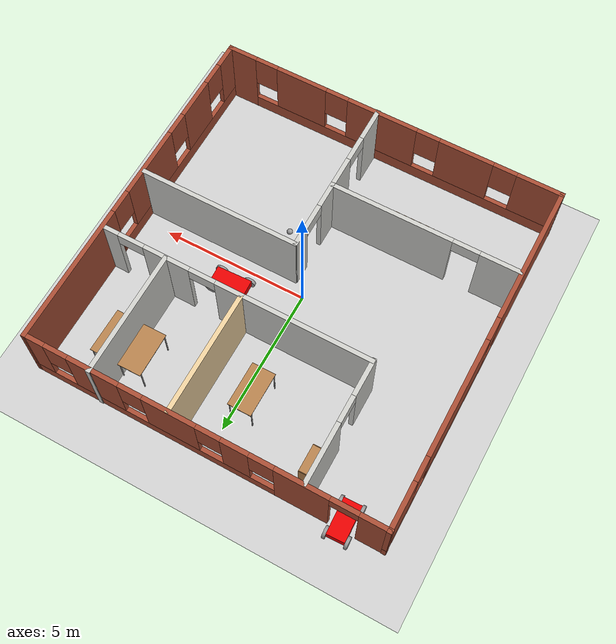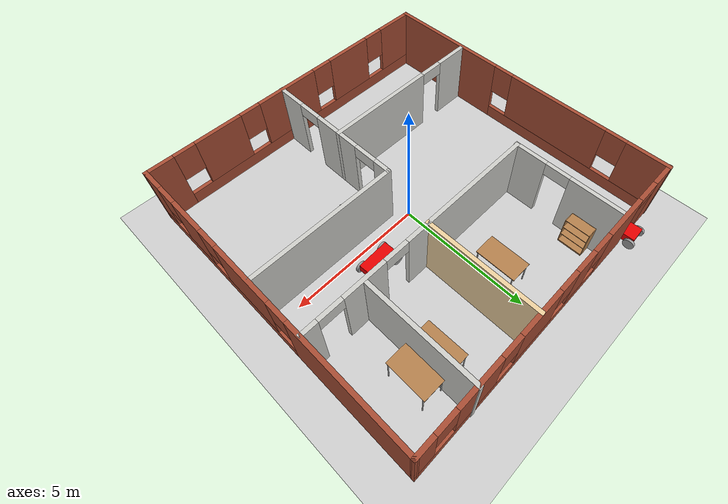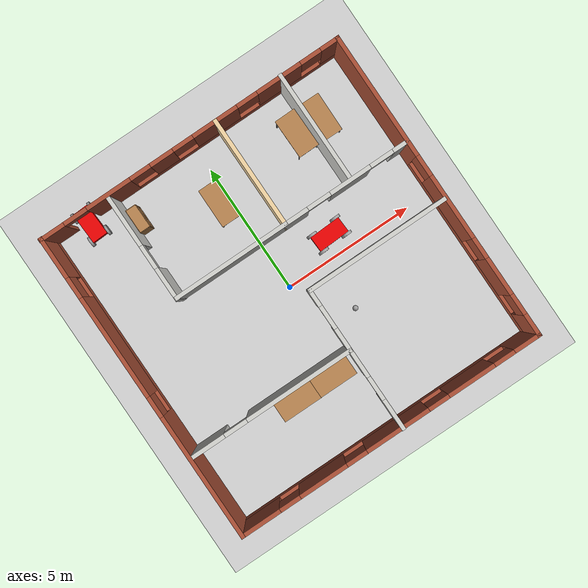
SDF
<sdf version="1.6">
 <world name="office">
  <plugin name="welcome_message" filename="libwelcome_message.so"/>
  <light name="sun" type="directional">
   <pose>0 0 10 0 -0 0</pose>
   <diffuse>0.8 0.8 0.8 1</diffuse>
   <specular>0.2 0.2 0.2 1</specular>
   <attenuation>
    <range>1000</range>
    <constant>0.9</constant>
    <linear>0.01</linear>
    <quadratic>0.001</quadratic>
   </attenuation>
   <direction>-0.5 0.1 -0.9</direction>
  </light>
  <model name="ground_plane">
   <static>1</static>
   <link name="link">
    <collision name="collision">
     <geometry><plane><normal>0 0 1</normal><size>100 100</size></plane></geometry>
     <surface><friction><ode><mu>100</mu><mu2>50</mu2></ode></friction></surface>
    </collision>
    <visual name="visual">
     <cast_shadows>0</cast_shadows>
     <geometry><plane><normal>0 0 1</normal><size>100 100</size></plane></geometry>
     <material>
      <script><uri>file://media/materials/scripts/gazebo.material</uri><name>Gazebo/Grey</name></script>
     </material>
    </visual>
   </link>
  </model>
  <gravity>0 0 -9.8</gravity>
  <magnetic_field>6e-06 2.3e-05 -4.2e-05</magnetic_field>
  <atmosphere type="adiabatic"/>
  <physics name="default_physics" default="0" type="ode">
   <max_step_size>0.001</max_step_size>
   <real_time_factor>1</real_time_factor>
   <real_time_update_rate>1000</real_time_update_rate>
  </physics>
  <scene><ambient>0.4 0.4 0.4 1</ambient><background>0.7 0.7 0.7 1</background><shadows>1</shadows></scene>
  <spherical_coordinates>
   <surface_model>EARTH_WGS84</surface_model>
   <latitude_deg>0</latitude_deg>
   <longitude_deg>0</longitude_deg>
   <elevation>0</elevation>
   <heading_deg>0</heading_deg>
  </spherical_coordinates>
  <model name="car">
   <pose>-4.53314 5.76816 0.211113 2e-06 1e-06 -1.53251</pose>
   <link name="link_0">
    <pose>0 -2e-06 0.088889 0 -0 0</pose>
    <inertial>
     <mass>1</mass>
     <inertia>
      <ixx>0.166667</ixx>
      <ixy>0</ixy>
      <ixz>0</ixz>
      <iyy>0.166667</iyy>
      <iyz>0</iyz>
      <izz>0.166667</izz>
     </inertia>
    </inertial>
    <visual name="visual">
     <geometry><box><size>1.2 0.6 0.3</size></box></geometry>
     <material>
      <lighting>1</lighting>
      <script><uri>file://media/materials/scripts/gazebo.material</uri><name>Gazebo/Grey</name></script>
      <shader type="pixel"><normal_map>__default__</normal_map></shader>
      <ambient>0.9 0 0 1</ambient>
      <diffuse>0.7 0.7 0.7 1</diffuse>
      <specular>0.01 0.01 0.01 1</specular>
      <emissive>0 0 0 1</emissive>
     </material>
    </visual>
    <collision name="collision">
     <geometry><box><size>1.2 0.6 0.3</size></box></geometry>
     <surface>
      <friction>
       <ode><mu>1</mu><mu2>1</mu2><fdir1>0 0 0</fdir1><slip1>0</slip1><slip2>0</slip2></ode>
       <torsional>
        <coefficient>1</coefficient>
        <patch_radius>0</patch_radius>
        <surface_radius>0</surface_radius>
        <use_patch_radius>1</use_patch_radius>
        <ode><slip>0</slip></ode>
       </torsional>
      </friction>
      <bounce><restitution_coefficient>0</restitution_coefficient><threshold>1e+06</threshold></bounce>
      <contact>
       <collide_without_contact>0</collide_without_contact>
       <collide_without_contact_bitmask>1</collide_without_contact_bitmask>
       <collide_bitmask>1</collide_bitmask>
       <ode>
        <soft_cfm>0</soft_cfm>
        <soft_erp>0.2</soft_erp>
        <kp>1e+13</kp>
        <kd>1</kd>
        <max_vel>0.01</max_vel>
        <min_depth>0</min_depth>
       </ode>
       <bullet>
        <split_impulse>1</split_impulse>
        <split_impulse_penetration_threshold>-0.01</split_impulse_penetration_threshold>
        <soft_cfm>0</soft_cfm>
        <soft_erp>0.2</soft_erp>
        <kp>1e+13</kp>
        <kd>1</kd>
       </bullet>
      </contact>
     </surface>
    </collision>
   </link>
   <link name="link_1">
    <pose>-0.5 -0.250002 -0.011111 0 -0 0</pose>
    <inertial>
     <mass>1</mass>
     <inertia>
      <ixx>0.166667</ixx>
      <ixy>0</ixy>
      <ixz>0</ixz>
      <iyy>0.166667</iyy>
      <iyz>0</iyz>
      <izz>0.166667</izz>
     </inertia>
    </inertial>
    <visual name="visual">
     <geometry><box><size>0.1 0.1 0.1</size></box></geometry>
     <material>
      <lighting>1</lighting>
      <script><uri>file://media/materials/scripts/gazebo.material</uri><name>Gazebo/Grey</name></script>
      <shader type="pixel"><normal_map>__default__</normal_map></shader>
      <ambient>0.01 0.01 0.01 1</ambient>
      <diffuse>0.7 0.7 0.7 1</diffuse>
      <specular>0.01 0.01 0.01 1</specular>
      <emissive>0 0 0 1</emissive>
     </material>
    </visual>
    <collision name="collision">
     <geometry><box><size>0.1 0.1 0.1</size></box></geometry>
     <surface>
      <friction>
       <ode><mu>1</mu><mu2>1</mu2><fdir1>0 0 0</fdir1><slip1>0</slip1><slip2>0</slip2></ode>
       <torsional>
        <coefficient>1</coefficient>
        <patch_radius>0</patch_radius>
        <surface_radius>0</surface_radius>
        <use_patch_radius>1</use_patch_radius>
        <ode><slip>0</slip></ode>
       </torsional>
      </friction>
      <bounce><restitution_coefficient>0</restitution_coefficient><threshold>1e+06</threshold></bounce>
      <contact>
       <collide_without_contact>0</collide_without_contact>
       <collide_without_contact_bitmask>1</collide_without_contact_bitmask>
       <collide_bitmask>1</collide_bitmask>
       <ode>
        <soft_cfm>0</soft_cfm>
        <soft_erp>0.2</soft_erp>
        <kp>1e+13</kp>
        <kd>1</kd>
        <max_vel>0.01</max_vel>
        <min_depth>0</min_depth>
       </ode>
       <bullet>
        <split_impulse>1</split_impulse>
        <split_impulse_penetration_threshold>-0.01</split_impulse_penetration_threshold>
        <soft_cfm>0</soft_cfm>
        <soft_erp>0.2</soft_erp>
        <kp>1e+13</kp>
        <kd>1</kd>
       </bullet>
      </contact>
     </surface>
    </collision>
   </link>
   <link name="link_1_clone">
    <pose>-0.5 0.249998 -0.011111 0 -0 0</pose>
    <inertial>
     <mass>1</mass>
     <inertia>
      <ixx>0.166667</ixx>
      <ixy>0</ixy>
      <ixz>0</ixz>
      <iyy>0.166667</iyy>
      <iyz>0</iyz>
      <izz>0.166667</izz>
     </inertia>
    </inertial>
    <visual name="visual">
     <geometry><box><size>0.1 0.1 0.1</size></box></geometry>
     <material>
      <lighting>1</lighting>
      <script><uri>file://media/materials/scripts/gazebo.material</uri><name>Gazebo/Grey</name></script>
      <shader type="pixel"><normal_map>__default__</normal_map></shader>
      <ambient>0.01 0.01 0.01 1</ambient>
      <diffuse>0.7 0.7 0.7 1</diffuse>
      <specular>0.01 0.01 0.01 1</specular>
      <emissive>0 0 0 1</emissive>
     </material>
    </visual>
    <collision name="collision">
     <geometry><box><size>0.1 0.1 0.1</size></box></geometry>
     <surface>
      <friction>
       <ode><mu>1</mu><mu2>1</mu2><fdir1>0 0 0</fdir1><slip1>0</slip1><slip2>0</slip2></ode>
       <torsional>
        <coefficient>1</coefficient>
        <patch_radius>0</patch_radius>
        <surface_radius>0</surface_radius>
        <use_patch_radius>1</use_patch_radius>
        <ode><slip>0</slip></ode>
       </torsional>
      </friction>
      <bounce><restitution_coefficient>0</restitution_coefficient><threshold>1e+06</threshold></bounce>
      <contact>
       <collide_without_contact>0</collide_without_contact>
       <collide_without_contact_bitmask>1</collide_without_contact_bitmask>
       <collide_bitmask>1</collide_bitmask>
       <ode>
        <soft_cfm>0</soft_cfm>
        <soft_erp>0.2</soft_erp>
        <kp>1e+13</kp>
        <kd>1</kd>
        <max_vel>0.01</max_vel>
        <min_depth>0</min_depth>
       </ode>
       <bullet>
        <split_impulse>1</split_impulse>
        <split_impulse_penetration_threshold>-0.01</split_impulse_penetration_threshold>
        <soft_cfm>0</soft_cfm>
        <soft_erp>0.2</soft_erp>
        <kp>1e+13</kp>
        <kd>1</kd>
       </bullet>
      </contact>
     </surface>
    </collision>
   </link>
   <link name="link_1_clone_0">
    <pose>0.5 -0.250002 -0.011111 0 -0 0</pose>
    <inertial>
     <mass>1</mass>
     <inertia>
      <ixx>0.166667</ixx>
      <ixy>0</ixy>
      <ixz>0</ixz>
      <iyy>0.166667</iyy>
      <iyz>0</iyz>
      <izz>0.166667</izz>
     </inertia>
    </inertial>
    <visual name="visual">
     <geometry><box><size>0.1 0.1 0.1</size></box></geometry>
     <material>
      <lighting>1</lighting>
      <script><uri>file://media/materials/scripts/gazebo.material</uri><name>Gazebo/Grey</name></script>
      <shader type="pixel"><normal_map>__default__</normal_map></shader>
      <ambient>0.01 0.01 0.01 1</ambient>
      <diffuse>0.7 0.7 0.7 1</diffuse>
      <specular>0.01 0.01 0.01 1</specular>
      <emissive>0 0 0 1</emissive>
     </material>
    </visual>
    <collision name="collision">
     <geometry><box><size>0.1 0.1 0.1</size></box></geometry>
     <surface>
      <friction>
       <ode><mu>1</mu><mu2>1</mu2><fdir1>0 0 0</fdir1><slip1>0</slip1><slip2>0</slip2></ode>
       <torsional>
        <coefficient>1</coefficient>
        <patch_radius>0</patch_radius>
        <surface_radius>0</surface_radius>
        <use_patch_radius>1</use_patch_radius>
        <ode><slip>0</slip></ode>
       </torsional>
      </friction>
      <bounce><restitution_coefficient>0</restitution_coefficient><threshold>1e+06</threshold></bounce>
      <contact>
       <collide_without_contact>0</collide_without_contact>
       <collide_without_contact_bitmask>1</collide_without_contact_bitmask>
       <collide_bitmask>1</collide_bitmask>
       <ode>
        <soft_cfm>0</soft_cfm>
        <soft_erp>0.2</soft_erp>
        <kp>1e+13</kp>
        <kd>1</kd>
        <max_vel>0.01</max_vel>
        <min_depth>0</min_depth>
       </ode>
       <bullet>
        <split_impulse>1</split_impulse>
        <split_impulse_penetration_threshold>-0.01</split_impulse_penetration_threshold>
        <soft_cfm>0</soft_cfm>
        <soft_erp>0.2</soft_erp>
        <kp>1e+13</kp>
        <kd>1</kd>
       </bullet>
      </contact>
     </surface>
    </collision>
   </link>
   <link name="link_1_clone_1">
    <pose>0.5 0.249998 -0.011111 0 -0 0</pose>
    <inertial>
     <mass>1</mass>
     <inertia>
      <ixx>0.166667</ixx>
      <ixy>0</ixy>
      <ixz>0</ixz>
      <iyy>0.166667</iyy>
      <iyz>0</iyz>
      <izz>0.166667</izz>
     </inertia>
    </inertial>
    <visual name="visual">
     <geometry><box><size>0.1 0.1 0.1</size></box></geometry>
     <material>
      <lighting>1</lighting>
      <script><uri>file://media/materials/scripts/gazebo.material</uri><name>Gazebo/Grey</name></script>
      <shader type="pixel"><normal_map>__default__</normal_map></shader>
      <ambient>0.01 0.01 0.01 1</ambient>
      <diffuse>0.7 0.7 0.7 1</diffuse>
      <specular>0.01 0.01 0.01 1</specular>
      <emissive>0 0 0 1</emissive>
     </material>
    </visual>
    <collision name="collision">
     <geometry><box><size>0.1 0.1 0.1</size></box></geometry>
     <surface>
      <friction>
       <ode><mu>1</mu><mu2>1</mu2><fdir1>0 0 0</fdir1><slip1>0</slip1><slip2>0</slip2></ode>
       <torsional>
        <coefficient>1</coefficient>
        <patch_radius>0</patch_radius>
        <surface_radius>0</surface_radius>
        <use_patch_radius>1</use_patch_radius>
        <ode><slip>0</slip></ode>
       </torsional>
      </friction>
      <bounce><restitution_coefficient>0</restitution_coefficient><threshold>1e+06</threshold></bounce>
      <contact>
       <collide_without_contact>0</collide_without_contact>
       <collide_without_contact_bitmask>1</collide_without_contact_bitmask>
       <collide_bitmask>1</collide_bitmask>
       <ode>
        <soft_cfm>0</soft_cfm>
        <soft_erp>0.2</soft_erp>
        <kp>1e+13</kp>
        <kd>1</kd>
        <max_vel>0.01</max_vel>
        <min_depth>0</min_depth>
       </ode>
       <bullet>
        <split_impulse>1</split_impulse>
        <split_impulse_penetration_threshold>-0.01</split_impulse_penetration_threshold>
        <soft_cfm>0</soft_cfm>
        <soft_erp>0.2</soft_erp>
        <kp>1e+13</kp>
        <kd>1</kd>
       </bullet>
      </contact>
     </surface>
    </collision>
   </link>
   <link name="link_2">
    <pose>-0.5 -0.350002 -0.011111 0 -0 0</pose>
    <inertial>
     <mass>1</mass>
     <inertia><ixx>0.145833</ixx><ixy>0</ixy><ixz>0</ixz><iyy>0.145833</iyy><iyz>0</iyz><izz>0.125</izz></inertia>
    </inertial>
    <visual name="visual">
     <pose>0 0 0 1.5707 -0 0</pose>
     <geometry><cylinder><radius>0.2</radius><length>0.1</length></cylinder></geometry>
     <material>
      <lighting>1</lighting>
      <script><uri>file://media/materials/scripts/gazebo.material</uri><name>Gazebo/Grey</name></script>
      <shader type="pixel"><normal_map>__default__</normal_map></shader>
      <ambient>0.01 0.01 0.01 1</ambient>
      <diffuse>0.7 0.7 0.7 1</diffuse>
      <specular>0.01 0.01 0.01 1</specular>
      <emissive>0 0 0 1</emissive>
     </material>
    </visual>
    <collision name="collision">
     <pose>0 0 0 1.5707 -0 0</pose>
     <geometry><cylinder><radius>0.2</radius><length>0.1</length></cylinder></geometry>
     <surface>
      <friction>
       <ode><mu>1</mu><mu2>1</mu2><fdir1>0 0 0</fdir1><slip1>0</slip1><slip2>0</slip2></ode>
       <torsional>
        <coefficient>1</coefficient>
        <patch_radius>0</patch_radius>
        <surface_radius>0</surface_radius>
        <use_patch_radius>1</use_patch_radius>
        <ode><slip>0</slip></ode>
       </torsional>
      </friction>
      <bounce><restitution_coefficient>0</restitution_coefficient><threshold>1e+06</threshold></bounce>
      <contact>
       <collide_without_contact>0</collide_without_contact>
       <collide_without_contact_bitmask>1</collide_without_contact_bitmask>
       <collide_bitmask>1</collide_bitmask>
       <ode>
        <soft_cfm>0</soft_cfm>
        <soft_erp>0.2</soft_erp>
        <kp>1e+13</kp>
        <kd>1</kd>
        <max_vel>0.01</max_vel>
        <min_depth>0</min_depth>
       </ode>
       <bullet>
        <split_impulse>1</split_impulse>
        <split_impulse_penetration_threshold>-0.01</split_impulse_penetration_threshold>
        <soft_cfm>0</soft_cfm>
        <soft_erp>0.2</soft_erp>
        <kp>1e+13</kp>
        <kd>1</kd>
       </bullet>
      </contact>
     </surface>
    </collision>
   </link>
   <link name="link_2_clone">
    <pose>-0.5 0.349998 -0.011111 0 -0 0</pose>
    <inertial>
     <mass>1</mass>
     <inertia><ixx>0.145833</ixx><ixy>0</ixy><ixz>0</ixz><iyy>0.145833</iyy><iyz>0</iyz><izz>0.125</izz></inertia>
    </inertial>
    <visual name="visual">
     <pose>0 0 0 1.5707 -0 0</pose>
     <geometry><cylinder><radius>0.2</radius><length>0.1</length></cylinder></geometry>
     <material>
      <lighting>1</lighting>
      <script><uri>file://media/materials/scripts/gazebo.material</uri><name>Gazebo/Grey</name></script>
      <shader type="pixel"><normal_map>__default__</normal_map></shader>
      <ambient>0.01 0.01 0.01 1</ambient>
      <diffuse>0.7 0.7 0.7 1</diffuse>
      <specular>0.01 0.01 0.01 1</specular>
      <emissive>0 0 0 1</emissive>
     </material>
    </visual>
    <collision name="collision">
     <pose>0 0 0 1.5707 -0 0</pose>
     <geometry><cylinder><radius>0.2</radius><length>0.1</length></cylinder></geometry>
     <surface>
      <friction>
       <ode><mu>1</mu><mu2>1</mu2><fdir1>0 0 0</fdir1><slip1>0</slip1><slip2>0</slip2></ode>
       <torsional>
        <coefficient>1</coefficient>
        <patch_radius>0</patch_radius>
        <surface_radius>0</surface_radius>
        <use_patch_radius>1</use_patch_radius>
        <ode><slip>0</slip></ode>
       </torsional>
      </friction>
      <bounce><restitution_coefficient>0</restitution_coefficient><threshold>1e+06</threshold></bounce>
      <contact>
       <collide_without_contact>0</collide_without_contact>
       <collide_without_contact_bitmask>1</collide_without_contact_bitmask>
       <collide_bitmask>1</collide_bitmask>
       <ode>
        <soft_cfm>0</soft_cfm>
        <soft_erp>0.2</soft_erp>
        <kp>1e+13</kp>
        <kd>1</kd>
        <max_vel>0.01</max_vel>
        <min_depth>0</min_depth>
       </ode>
       <bullet>
        <split_impulse>1</split_impulse>
        <split_impulse_penetration_threshold>-0.01</split_impulse_penetration_threshold>
        <soft_cfm>0</soft_cfm>
        <soft_erp>0.2</soft_erp>
        <kp>1e+13</kp>
        <kd>1</kd>
       </bullet>
      </contact>
     </surface>
    </collision>
   </link>
   <link name="link_2_clone_0">
    <pose>0.5 -0.350021 -0.011111 0 -0 0</pose>
    <inertial>
     <mass>1</mass>
     <inertia><ixx>0.145833</ixx><ixy>0</ixy><ixz>0</ixz><iyy>0.145833</iyy><iyz>0</iyz><izz>0.125</izz></inertia>
    </inertial>
    <visual name="visual">
     <pose>0 0 0 1.5707 -0 0</pose>
     <geometry><cylinder><radius>0.2</radius><length>0.1</length></cylinder></geometry>
     <material>
      <lighting>1</lighting>
      <script><uri>file://media/materials/scripts/gazebo.material</uri><name>Gazebo/Grey</name></script>
      <shader type="pixel"><normal_map>__default__</normal_map></shader>
      <ambient>0.01 0.01 0.01 1</ambient>
      <diffuse>0.7 0.7 0.7 1</diffuse>
      <specular>0.01 0.01 0.01 1</specular>
      <emissive>0 0 0 1</emissive>
     </material>
    </visual>
    <collision name="collision">
     <pose>0 0 0 1.5707 -0 0</pose>
     <geometry><cylinder><radius>0.2</radius><length>0.1</length></cylinder></geometry>
     <surface>
      <friction>
       <ode><mu>1</mu><mu2>1</mu2><fdir1>0 0 0</fdir1><slip1>0</slip1><slip2>0</slip2></ode>
       <torsional>
        <coefficient>1</coefficient>
        <patch_radius>0</patch_radius>
        <surface_radius>0</surface_radius>
        <use_patch_radius>1</use_patch_radius>
        <ode><slip>0</slip></ode>
       </torsional>
      </friction>
      <bounce><restitution_coefficient>0</restitution_coefficient><threshold>1e+06</threshold></bounce>
      <contact>
       <collide_without_contact>0</collide_without_contact>
       <collide_without_contact_bitmask>1</collide_without_contact_bitmask>
       <collide_bitmask>1</collide_bitmask>
       <ode>
        <soft_cfm>0</soft_cfm>
        <soft_erp>0.2</soft_erp>
        <kp>1e+13</kp>
        <kd>1</kd>
        <max_vel>0.01</max_vel>
        <min_depth>0</min_depth>
       </ode>
       <bullet>
        <split_impulse>1</split_impulse>
        <split_impulse_penetration_threshold>-0.01</split_impulse_penetration_threshold>
        <soft_cfm>0</soft_cfm>
        <soft_erp>0.2</soft_erp>
        <kp>1e+13</kp>
        <kd>1</kd>
       </bullet>
      </contact>
     </surface>
    </collision>
   </link>
   <link name="link_2_clone_1">
    <pose>0.5 0.350017 -0.011111 0 -0 0</pose>
    <inertial>
     <mass>1</mass>
     <inertia><ixx>0.145833</ixx><ixy>0</ixy><ixz>0</ixz><iyy>0.145833</iyy><iyz>0</iyz><izz>0.125</izz></inertia>
    </inertial>
    <visual name="visual">
     <pose>0 0 0 1.5707 -0 0</pose>
     <geometry><cylinder><radius>0.2</radius><length>0.1</length></cylinder></geometry>
     <material>
      <lighting>1</lighting>
      <script><uri>file://media/materials/scripts/gazebo.material</uri><name>Gazebo/Grey</name></script>
      <shader type="pixel"><normal_map>__default__</normal_map></shader>
      <ambient>0.01 0.01 0.01 1</ambient>
      <diffuse>0.7 0.7 0.7 1</diffuse>
      <specular>0.01 0.01 0.01 1</specular>
      <emissive>0 0 0 1</emissive>
     </material>
    </visual>
    <collision name="collision">
     <pose>0 0 0 1.5707 -0 0</pose>
     <geometry><cylinder><radius>0.2</radius><length>0.1</length></cylinder></geometry>
     <surface>
      <friction>
       <ode><mu>1</mu><mu2>1</mu2><fdir1>0 0 0</fdir1><slip1>0</slip1><slip2>0</slip2></ode>
       <torsional>
        <coefficient>1</coefficient>
        <patch_radius>0</patch_radius>
        <surface_radius>0</surface_radius>
        <use_patch_radius>1</use_patch_radius>
        <ode><slip>0</slip></ode>
       </torsional>
      </friction>
      <bounce><restitution_coefficient>0</restitution_coefficient><threshold>1e+06</threshold></bounce>
      <contact>
       <collide_without_contact>0</collide_without_contact>
       <collide_without_contact_bitmask>1</collide_without_contact_bitmask>
       <collide_bitmask>1</collide_bitmask>
       <ode>
        <soft_cfm>0</soft_cfm>
        <soft_erp>0.2</soft_erp>
        <kp>1e+13</kp>
        <kd>1</kd>
        <max_vel>0.01</max_vel>
        <min_depth>0</min_depth>
       </ode>
       <bullet>
        <split_impulse>1</split_impulse>
        <split_impulse_penetration_threshold>-0.01</split_impulse_penetration_threshold>
        <soft_cfm>0</soft_cfm>
        <soft_erp>0.2</soft_erp>
        <kp>1e+13</kp>
        <kd>1</kd>
       </bullet>
      </contact>
     </surface>
    </collision>
   </link>
   <joint name="link_0_JOINT_0" type="fixed">
    <parent>link_0</parent>
    <child>link_1</child>
    <physics>
     <ode><limit><cfm>0</cfm><erp>0.2</erp></limit><suspension><cfm>0</cfm><erp>0.2</erp></suspension></ode>
    </physics>
   </joint>
   <joint name="link_0_JOINT_1" type="fixed">
    <parent>link_0</parent>
    <child>link_1_clone</child>
    <physics>
     <ode><limit><cfm>0</cfm><erp>0.2</erp></limit><suspension><cfm>0</cfm><erp>0.2</erp></suspension></ode>
    </physics>
   </joint>
   <joint name="link_0_JOINT_2" type="fixed">
    <parent>link_0</parent>
    <child>link_1_clone_0</child>
    <physics>
     <ode><limit><cfm>0</cfm><erp>0.2</erp></limit><suspension><cfm>0</cfm><erp>0.2</erp></suspension></ode>
    </physics>
   </joint>
   <joint name="link_0_JOINT_3" type="fixed">
    <parent>link_0</parent>
    <child>link_1_clone_1</child>
    <physics>
     <ode><limit><cfm>0</cfm><erp>0.2</erp></limit><suspension><cfm>0</cfm><erp>0.2</erp></suspension></ode>
    </physics>
   </joint>
   <joint name="link_1_JOINT_4" type="revolute">
    <parent>link_1</parent>
    <child>link_2</child>
    <axis>
     <xyz>0 1 0</xyz>
     <use_parent_model_frame>0</use_parent_model_frame>
     <limit>
      <lower>-1.79769e+308</lower>
      <upper>1.79769e+308</upper>
      <effort>-1</effort>
      <velocity>-1</velocity>
     </limit>
     <dynamics>
      <spring_reference>0</spring_reference>
      <spring_stiffness>0</spring_stiffness>
      <damping>0</damping>
      <friction>0</friction>
     </dynamics>
    </axis>
    <physics>
     <ode><limit><cfm>0</cfm><erp>0.2</erp></limit><suspension><cfm>0</cfm><erp>0.2</erp></suspension></ode>
    </physics>
   </joint>
   <joint name="link_1_clone_0_JOINT_7" type="revolute">
    <parent>link_1_clone_0</parent>
    <child>link_2_clone_0</child>
    <axis>
     <xyz>0 1 0</xyz>
     <use_parent_model_frame>0</use_parent_model_frame>
     <limit>
      <lower>-1.79769e+308</lower>
      <upper>1.79769e+308</upper>
      <effort>-1</effort>
      <velocity>-1</velocity>
     </limit>
     <dynamics>
      <spring_reference>0</spring_reference>
      <spring_stiffness>0</spring_stiffness>
      <damping>0</damping>
     </dynamics>
    </axis>
    <physics>
     <ode><limit><cfm>0</cfm><erp>0.2</erp></limit><suspension><cfm>0</cfm><erp>0.2</erp></suspension></ode>
    </physics>
   </joint>
   <joint name="link_1_clone_1_JOINT_8" type="revolute">
    <parent>link_1_clone_1</parent>
    <child>link_2_clone_1</child>
    <pose>0 0 0 0 0.03 0.02</pose>
    <axis>
     <xyz>0 1 0</xyz>
     <use_parent_model_frame>0</use_parent_model_frame>
     <limit>
      <lower>-1.79769e+308</lower>
      <upper>1.79769e+308</upper>
      <effort>-1</effort>
      <velocity>-1</velocity>
     </limit>
     <dynamics>
      <spring_reference>0</spring_reference>
      <spring_stiffness>0</spring_stiffness>
      <damping>0</damping>
      <friction>0</friction>
     </dynamics>
    </axis>
    <physics>
     <ode><limit><cfm>0</cfm><erp>0.2</erp></limit><suspension><cfm>0</cfm><erp>0.2</erp></suspension></ode>
    </physics>
   </joint>
   <joint name="link_1_clone_JOINT_6" type="revolute">
    <parent>link_1_clone</parent>
    <child>link_2_clone</child>
    <axis>
     <xyz>0 1 0</xyz>
     <use_parent_model_frame>0</use_parent_model_frame>
     <limit>
      <lower>-1.79769e+308</lower>
      <upper>1.79769e+308</upper>
      <effort>-1</effort>
      <velocity>-1</velocity>
     </limit>
     <dynamics>
      <spring_reference>0</spring_reference>
      <spring_stiffness>0</spring_stiffness>
      <damping>0</damping>
     </dynamics>
    </axis>
    <physics>
     <ode><limit><cfm>0</cfm><erp>0.2</erp></limit><suspension><cfm>0</cfm><erp>0.2</erp></suspension></ode>
    </physics>
   </joint>
   <static>0</static>
  </model>
  <model name="building">
   <pose>-0.00035 0.007797 0 0 -0 0</pose>
   <link name="Wall_0">
    <pose>-5.91755 0.003133 0 0 -0 1.5708</pose>
    <visual name="Wall_0_Visual_0">
     <pose>-3.58906 0 1.25 0 -0 0</pose>
     <geometry><box><size>4.82188 0.15 2.5</size></box></geometry>
     <material>
      <script><uri>file://media/materials/scripts/gazebo.material</uri><name>Gazebo/Bricks</name></script>
      <ambient>1 1 1 1</ambient>
     </material>
     <meta><layer>0</layer></meta>
    </visual>
    <collision name="Wall_0_Collision_0">
     <geometry><box><size>4.82188 0.15 2.5</size></box></geometry>
     <pose>-3.58906 0 1.25 0 -0 0</pose>
    </collision>
    <visual name="Wall_0_Visual_1">
     <pose>2.41094 0 0.25 0 -0 0</pose>
     <geometry><box><size>7.17812 0.15 0.5</size></box></geometry>
     <material>
      <script><uri>file://media/materials/scripts/gazebo.material</uri><name>Gazebo/Bricks</name></script>
      <ambient>1 1 1 1</ambient>
     </material>
     <meta><layer>0</layer></meta>
    </visual>
    <collision name="Wall_0_Collision_1">
     <geometry><box><size>7.17812 0.15 0.5</size></box></geometry>
     <pose>2.41094 0 0.25 0 -0 0</pose>
    </collision>
    <visual name="Wall_0_Visual_2">
     <pose>1.60287 0 1.5 0 -0 0</pose>
     <geometry><box><size>3.96196 0.15 2</size></box></geometry>
     <material>
      <script><uri>file://media/materials/scripts/gazebo.material</uri><name>Gazebo/Bricks</name></script>
      <ambient>1 1 1 1</ambient>
     </material>
     <meta><layer>0</layer></meta>
    </visual>
    <collision name="Wall_0_Collision_2">
     <geometry><box><size>3.96196 0.15 2</size></box></geometry>
     <pose>1.60287 0 1.5 0 -0 0</pose>
    </collision>
    <visual name="Wall_0_Visual_3">
     <pose>5.19192 0 1.5 0 -0 0</pose>
     <geometry><box><size>1.61615 0.15 2</size></box></geometry>
     <material>
      <script><uri>file://media/materials/scripts/gazebo.material</uri><name>Gazebo/Bricks</name></script>
      <ambient>1 1 1 1</ambient>
     </material>
     <meta><layer>0</layer></meta>
    </visual>
    <collision name="Wall_0_Collision_3">
     <geometry><box><size>1.61615 0.15 2</size></box></geometry>
     <pose>5.19192 0 1.5 0 -0 0</pose>
    </collision>
    <visual name="Wall_0_Visual_4">
     <pose>-0.778116 0 1.9 0 -0 0</pose>
     <geometry><box><size>0.8 0.15 1.2</size></box></geometry>
     <material>
      <script><uri>file://media/materials/scripts/gazebo.material</uri><name>Gazebo/Bricks</name></script>
      <ambient>1 1 1 1</ambient>
     </material>
     <meta><layer>0</layer></meta>
    </visual>
    <collision name="Wall_0_Collision_4">
     <geometry><box><size>0.8 0.15 1.2</size></box></geometry>
     <pose>-0.778116 0 1.9 0 -0 0</pose>
    </collision>
    <visual name="Wall_0_Visual_5">
     <pose>3.98385 0 1.9 0 -0 0</pose>
     <geometry><box><size>0.8 0.15 1.2</size></box></geometry>
     <material>
      <script><uri>file://media/materials/scripts/gazebo.material</uri><name>Gazebo/Bricks</name></script>
      <ambient>1 1 1 1</ambient>
     </material>
     <meta><layer>0</layer></meta>
    </visual>
    <collision name="Wall_0_Collision_5">
     <geometry><box><size>0.8 0.15 1.2</size></box></geometry>
     <pose>3.98385 0 1.9 0 -0 0</pose>
    </collision>
   </link>
   <link name="Wall_10">
    <collision name="Wall_10_Collision">
     <geometry><box><size>4.48462 0.15 2.5</size></box></geometry>
     <pose>0 0 1.25 0 -0 0</pose>
    </collision>
    <visual name="Wall_10_Visual">
     <pose>0 0 1.25 0 -0 0</pose>
     <geometry><box><size>4.48462 0.15 2.5</size></box></geometry>
     <material>
      <script><uri>file://media/materials/scripts/gazebo.material</uri><name>Gazebo/CeilingTiled</name></script>
      <ambient>0.921569 0.807843 0.615686 1</ambient>
     </material>
     <meta><layer>0</layer></meta>
    </visual>
    <pose>-1.11979 1.80988 0 0 -0 0</pose>
   </link>
   <link name="Wall_11">
    <collision name="Wall_11_Collision">
     <geometry><box><size>4.25 0.15 2.5</size></box></geometry>
     <pose>0 0 1.25 0 -0 0</pose>
    </collision>
    <visual name="Wall_11_Visual">
     <pose>0 0 1.25 0 -0 0</pose>
     <geometry><box><size>4.25 0.15 2.5</size></box></geometry>
     <material>
      <script><uri>file://media/materials/scripts/gazebo.material</uri><name>Gazebo/Grey</name></script>
      <ambient>0.921569 0.807843 0.615686 1</ambient>
     </material>
     <meta><layer>0</layer></meta>
    </visual>
    <pose>1.04751 3.85988 0 0 -0 1.5708</pose>
   </link>
   <link name="Wall_15">
    <pose>3.47252 1.80988 0 0 -0 0</pose>
    <visual name="Wall_15_Visual_0">
     <pose>-2.01342 0 1.25 0 -0 0</pose>
     <geometry><box><size>0.973156 0.15 2.5</size></box></geometry>
     <material>
      <script><uri>file://media/materials/scripts/gazebo.material</uri><name>Gazebo/CeilingTiled</name></script>
      <ambient>0.996078 0.47451 0.0196078 1</ambient>
     </material>
     <meta><layer>0</layer></meta>
    </visual>
    <collision name="Wall_15_Collision_0">
     <geometry><box><size>0.973156 0.15 2.5</size></box></geometry>
     <pose>-2.01342 0 1.25 0 -0 0</pose>
    </collision>
    <visual name="Wall_15_Visual_1">
     <pose>0.174229 0 1.25 0 -0 0</pose>
     <geometry><box><size>1.60215 0.15 2.5</size></box></geometry>
     <material>
      <script><uri>file://media/materials/scripts/gazebo.material</uri><name>Gazebo/CeilingTiled</name></script>
      <ambient>0.996078 0.47451 0.0196078 1</ambient>
     </material>
     <meta><layer>0</layer></meta>
    </visual>
    <collision name="Wall_15_Collision_1">
     <geometry><box><size>1.60215 0.15 2.5</size></box></geometry>
     <pose>0.174229 0 1.25 0 -0 0</pose>
    </collision>
    <visual name="Wall_15_Visual_2">
     <pose>2.18765 0 1.25 0 -0 0</pose>
     <geometry><box><size>0.624697 0.15 2.5</size></box></geometry>
     <material>
      <script><uri>file://media/materials/scripts/gazebo.material</uri><name>Gazebo/CeilingTiled</name></script>
      <ambient>0.996078 0.47451 0.0196078 1</ambient>
     </material>
     <meta><layer>0</layer></meta>
    </visual>
    <collision name="Wall_15_Collision_2">
     <geometry><box><size>0.624697 0.15 2.5</size></box></geometry>
     <pose>2.18765 0 1.25 0 -0 0</pose>
    </collision>
    <visual name="Wall_15_Visual_3">
     <pose>-1.07684 0 2.25 0 -0 0</pose>
     <geometry><box><size>0.9 0.15 0.5</size></box></geometry>
     <material>
      <script><uri>file://media/materials/scripts/gazebo.material</uri><name>Gazebo/CeilingTiled</name></script>
      <ambient>0.996078 0.47451 0.0196078 1</ambient>
     </material>
     <meta><layer>0</layer></meta>
    </visual>
    <collision name="Wall_15_Collision_3">
     <geometry><box><size>0.9 0.15 0.5</size></box></geometry>
     <pose>-1.07684 0 2.25 0 -0 0</pose>
    </collision>
    <visual name="Wall_15_Visual_4">
     <pose>1.4253 0 2.25 0 -0 0</pose>
     <geometry><box><size>0.9 0.15 0.5</size></box></geometry>
     <material>
      <script><uri>file://media/materials/scripts/gazebo.material</uri><name>Gazebo/CeilingTiled</name></script>
      <ambient>0.996078 0.47451 0.0196078 1</ambient>
     </material>
     <meta><layer>0</layer></meta>
    </visual>
    <collision name="Wall_15_Collision_4">
     <geometry><box><size>0.9 0.15 0.5</size></box></geometry>
     <pose>1.4253 0 2.25 0 -0 0</pose>
    </collision>
   </link>
   <link name="Wall_17">
    <collision name="Wall_17_Collision">
     <geometry><box><size>4.25 0.15 2.5</size></box></geometry>
     <pose>0 0 1.25 0 -0 0</pose>
    </collision>
    <visual name="Wall_17_Visual">
     <pose>0 0 1.25 0 -0 0</pose>
     <geometry><box><size>4.25 0.15 2.5</size></box></geometry>
     <material>
      <script><uri>file://media/materials/scripts/gazebo.material</uri><name>Gazebo/CeilingTiled</name></script>
      <ambient>0.996078 0.47451 0.0196078 1</ambient>
     </material>
     <meta><layer>0</layer></meta>
    </visual>
    <pose>3.6718 3.89596 0 0 0 -1.5708</pose>
   </link>
   <link name="Wall_2">
    <pose>0 5.91836 0 0 -0 0.000595</pose>
    <visual name="Wall_2_Visual_0">
     <pose>-5.50579 0 1.25 0 -0 0</pose>
     <geometry><box><size>1.00011 0.15 2.5</size></box></geometry>
     <material>
      <script><uri>file://media/materials/scripts/gazebo.material</uri><name>Gazebo/Bricks</name></script>
      <ambient>0.921569 0.807843 0.615686 1</ambient>
     </material>
     <meta><layer>0</layer></meta>
    </visual>
    <collision name="Wall_2_Collision_0">
     <geometry><box><size>1.00011 0.15 2.5</size></box></geometry>
     <pose>-5.50579 0 1.25 0 -0 0</pose>
    </collision>
    <visual name="Wall_2_Visual_1">
     <pose>-3.235 0 1.25 0 -0 0</pose>
     <geometry><box><size>1.74147 0.15 2.5</size></box></geometry>
     <material>
      <script><uri>file://media/materials/scripts/gazebo.material</uri><name>Gazebo/Bricks</name></script>
      <ambient>0.921569 0.807843 0.615686 1</ambient>
     </material>
     <meta><layer>0</layer></meta>
    </visual>
    <collision name="Wall_2_Collision_1">
     <geometry><box><size>1.74147 0.15 2.5</size></box></geometry>
     <pose>-3.235 0 1.25 0 -0 0</pose>
    </collision>
    <visual name="Wall_2_Visual_2">
     <pose>1.82079 0 0.25 0 -0 0</pose>
     <geometry><box><size>8.37012 0.15 0.5</size></box></geometry>
     <material>
      <script><uri>file://media/materials/scripts/gazebo.material</uri><name>Gazebo/Bricks</name></script>
      <ambient>0.921569 0.807843 0.615686 1</ambient>
     </material>
     <meta><layer>0</layer></meta>
    </visual>
    <collision name="Wall_2_Collision_2">
     <geometry><box><size>8.37012 0.15 0.5</size></box></geometry>
     <pose>1.82079 0 0.25 0 -0 0</pose>
    </collision>
    <visual name="Wall_2_Visual_3">
     <pose>-1.1134 0 1.5 0 -0 0</pose>
     <geometry><box><size>0.901735 0.15 2</size></box></geometry>
     <material>
      <script><uri>file://media/materials/scripts/gazebo.material</uri><name>Gazebo/Bricks</name></script>
      <ambient>0.921569 0.807843 0.615686 1</ambient>
     </material>
     <meta><layer>0</layer></meta>
    </visual>
    <collision name="Wall_2_Collision_3">
     <geometry><box><size>0.901735 0.15 2</size></box></geometry>
     <pose>-1.1134 0 1.5 0 -0 0</pose>
    </collision>
    <visual name="Wall_2_Visual_4">
     <pose>1.02146 0 1.5 0 -0 0</pose>
     <geometry><box><size>1.76798 0.15 2</size></box></geometry>
     <material>
      <script><uri>file://media/materials/scripts/gazebo.material</uri><name>Gazebo/Bricks</name></script>
      <ambient>0.921569 0.807843 0.615686 1</ambient>
     </material>
     <meta><layer>0</layer></meta>
    </visual>
    <collision name="Wall_2_Collision_4">
     <geometry><box><size>1.76798 0.15 2</size></box></geometry>
     <pose>1.02146 0 1.5 0 -0 0</pose>
    </collision>
    <visual name="Wall_2_Visual_5">
     <pose>3.57391 0 1.5 0 -0 0</pose>
     <geometry><box><size>1.73691 0.15 2</size></box></geometry>
     <material>
      <script><uri>file://media/materials/scripts/gazebo.material</uri><name>Gazebo/Bricks</name></script>
      <ambient>0.921569 0.807843 0.615686 1</ambient>
     </material>
     <meta><layer>0</layer></meta>
    </visual>
    <collision name="Wall_2_Collision_5">
     <geometry><box><size>1.73691 0.15 2</size></box></geometry>
     <pose>3.57391 0 1.5 0 -0 0</pose>
    </collision>
    <visual name="Wall_2_Visual_6">
     <pose>5.62411 0 1.5 0 -0 0</pose>
     <geometry><box><size>0.763489 0.15 2</size></box></geometry>
     <material>
      <script><uri>file://media/materials/scripts/gazebo.material</uri><name>Gazebo/Bricks</name></script>
      <ambient>0.921569 0.807843 0.615686 1</ambient>
     </material>
     <meta><layer>0</layer></meta>
    </visual>
    <collision name="Wall_2_Collision_6">
     <geometry><box><size>0.763489 0.15 2</size></box></geometry>
     <pose>5.62411 0 1.5 0 -0 0</pose>
    </collision>
    <visual name="Wall_2_Visual_7">
     <pose>-1.96426 0 1.9 0 -0 0</pose>
     <geometry><box><size>0.8 0.15 1.2</size></box></geometry>
     <material>
      <script><uri>file://media/materials/scripts/gazebo.material</uri><name>Gazebo/Bricks</name></script>
      <ambient>0.921569 0.807843 0.615686 1</ambient>
     </material>
     <meta><layer>0</layer></meta>
    </visual>
    <collision name="Wall_2_Collision_7">
     <geometry><box><size>0.8 0.15 1.2</size></box></geometry>
     <pose>-1.96426 0 1.9 0 -0 0</pose>
    </collision>
    <visual name="Wall_2_Visual_8">
     <pose>-0.26253 0 1.9 0 -0 0</pose>
     <geometry><box><size>0.8 0.15 1.2</size></box></geometry>
     <material>
      <script><uri>file://media/materials/scripts/gazebo.material</uri><name>Gazebo/Bricks</name></script>
      <ambient>0.921569 0.807843 0.615686 1</ambient>
     </material>
     <meta><layer>0</layer></meta>
    </visual>
    <collision name="Wall_2_Collision_8">
     <geometry><box><size>0.8 0.15 1.2</size></box></geometry>
     <pose>-0.26253 0 1.9 0 -0 0</pose>
    </collision>
    <visual name="Wall_2_Visual_9">
     <pose>2.30545 0 1.9 0 -0 0</pose>
     <geometry><box><size>0.8 0.15 1.2</size></box></geometry>
     <material>
      <script><uri>file://media/materials/scripts/gazebo.material</uri><name>Gazebo/Bricks</name></script>
      <ambient>0.921569 0.807843 0.615686 1</ambient>
     </material>
     <meta><layer>0</layer></meta>
    </visual>
    <collision name="Wall_2_Collision_9">
     <geometry><box><size>0.8 0.15 1.2</size></box></geometry>
     <pose>2.30545 0 1.9 0 -0 0</pose>
    </collision>
    <visual name="Wall_2_Visual_10">
     <pose>4.84236 0 1.9 0 -0 0</pose>
     <geometry><box><size>0.8 0.15 1.2</size></box></geometry>
     <material>
      <script><uri>file://media/materials/scripts/gazebo.material</uri><name>Gazebo/Bricks</name></script>
      <ambient>0.921569 0.807843 0.615686 1</ambient>
     </material>
     <meta><layer>0</layer></meta>
    </visual>
    <collision name="Wall_2_Collision_10">
     <geometry><box><size>0.8 0.15 1.2</size></box></geometry>
     <pose>4.84236 0 1.9 0 -0 0</pose>
    </collision>
    <visual name="Wall_2_Visual_11">
     <pose>-4.55574 0 2.25 0 -0 0</pose>
     <geometry><box><size>0.9 0.15 0.5</size></box></geometry>
     <material>
      <script><uri>file://media/materials/scripts/gazebo.material</uri><name>Gazebo/Bricks</name></script>
      <ambient>0.921569 0.807843 0.615686 1</ambient>
     </material>
     <meta><layer>0</layer></meta>
    </visual>
    <collision name="Wall_2_Collision_11">
     <geometry><box><size>0.9 0.15 0.5</size></box></geometry>
     <pose>-4.55574 0 2.25 0 -0 0</pose>
    </collision>
   </link>
   <link name="Wall_20">
    <pose>-2.69192 -2.84596 0 0 -0 0</pose>
    <visual name="Wall_20_Visual_0">
     <pose>-2.55329 0 1.25 0 -0 0</pose>
     <geometry><box><size>1.39341 0.15 2.5</size></box></geometry>
     <material>
      <script><uri>file://media/materials/scripts/gazebo.material</uri><name>Gazebo/CeilingTiled</name></script>
      <ambient>1 0.764706 0.305882 1</ambient>
     </material>
     <meta><layer>0</layer></meta>
    </visual>
    <collision name="Wall_20_Collision_0">
     <geometry><box><size>1.39341 0.15 2.5</size></box></geometry>
     <pose>-2.55329 0 1.25 0 -0 0</pose>
    </collision>
    <visual name="Wall_20_Visual_1">
     <pose>1.14671 0 1.25 0 -0 0</pose>
     <geometry><box><size>4.20659 0.15 2.5</size></box></geometry>
     <material>
      <script><uri>file://media/materials/scripts/gazebo.material</uri><name>Gazebo/CeilingTiled</name></script>
      <ambient>1 0.764706 0.305882 1</ambient>
     </material>
     <meta><layer>0</layer></meta>
    </visual>
    <collision name="Wall_20_Collision_1">
     <geometry><box><size>4.20659 0.15 2.5</size></box></geometry>
     <pose>1.14671 0 1.25 0 -0 0</pose>
    </collision>
    <visual name="Wall_20_Visual_2">
     <pose>-1.40659 0 2.25 0 -0 0</pose>
     <geometry><box><size>0.9 0.15 0.5</size></box></geometry>
     <material>
      <script><uri>file://media/materials/scripts/gazebo.material</uri><name>Gazebo/CeilingTiled</name></script>
      <ambient>1 0.764706 0.305882 1</ambient>
     </material>
     <meta><layer>0</layer></meta>
    </visual>
    <collision name="Wall_20_Collision_2">
     <geometry><box><size>0.9 0.15 0.5</size></box></geometry>
     <pose>-1.40659 0 2.25 0 -0 0</pose>
    </collision>
   </link>
   <link name="Wall_21">
    <pose>0.483078 -4.39596 0 0 0 -1.5708</pose>
    <visual name="Wall_21_Visual_0">
     <pose>-1.05225 0 1.25 0 -0 0</pose>
     <geometry><box><size>1.14549 0.15 2.5</size></box></geometry>
     <material>
      <script><uri>file://media/materials/scripts/gazebo.material</uri><name>Gazebo/CeilingTiled</name></script>
      <ambient>0.435294 0.796078 0.67451 1</ambient>
     </material>
     <meta><layer>0</layer></meta>
    </visual>
    <collision name="Wall_21_Collision_0">
     <geometry><box><size>1.14549 0.15 2.5</size></box></geometry>
     <pose>-1.05225 0 1.25 0 -0 0</pose>
    </collision>
    <visual name="Wall_21_Visual_1">
     <pose>1.02275 0 1.25 0 -0 0</pose>
     <geometry><box><size>1.20451 0.15 2.5</size></box></geometry>
     <material>
      <script><uri>file://media/materials/scripts/gazebo.material</uri><name>Gazebo/CeilingTiled</name></script>
      <ambient>0.435294 0.796078 0.67451 1</ambient>
     </material>
     <meta><layer>0</layer></meta>
    </visual>
    <collision name="Wall_21_Collision_1">
     <geometry><box><size>1.20451 0.15 2.5</size></box></geometry>
     <pose>1.02275 0 1.25 0 -0 0</pose>
    </collision>
    <visual name="Wall_21_Visual_2">
     <pose>-0.029508 0 2.25 0 -0 0</pose>
     <geometry><box><size>0.9 0.15 0.5</size></box></geometry>
     <material>
      <script><uri>file://media/materials/scripts/gazebo.material</uri><name>Gazebo/CeilingTiled</name></script>
      <ambient>0.435294 0.796078 0.67451 1</ambient>
     </material>
     <meta><layer>0</layer></meta>
    </visual>
    <collision name="Wall_21_Collision_2">
     <geometry><box><size>0.9 0.15 0.5</size></box></geometry>
     <pose>-0.029508 0 2.25 0 -0 0</pose>
    </collision>
   </link>
   <link name="Wall_23">
    <collision name="Wall_23_Collision">
     <geometry><box><size>5.5 0.15 2.5</size></box></geometry>
     <pose>0 0 1.25 0 -0 0</pose>
    </collision>
    <visual name="Wall_23_Visual">
     <pose>0 0 1.25 0 -0 0</pose>
     <geometry><box><size>5.5 0.15 2.5</size></box></geometry>
     <material>
      <script><uri>file://media/materials/scripts/gazebo.material</uri><name>Gazebo/CeilingTiled</name></script>
      <ambient>0.435294 0.796078 0.67451 1</ambient>
     </material>
     <meta><layer>0</layer></meta>
    </visual>
    <pose>3.17532 -0.459711 0 0 -0 3.14159</pose>
   </link>
   <link name="Wall_25">
    <pose>0.483078 -1.67096 0 0 -0 1.5708</pose>
    <visual name="Wall_25_Visual_0">
     <pose>-0.782101 0 1.25 0 -0 0</pose>
     <geometry><box><size>0.935797 0.15 2.5</size></box></geometry>
     <material>
      <script><uri>file://media/materials/scripts/gazebo.material</uri><name>Gazebo/CeilingTiled</name></script>
      <ambient>0.435294 0.796078 0.67451 1</ambient>
     </material>
     <meta><layer>0</layer></meta>
    </visual>
    <collision name="Wall_25_Collision_0">
     <geometry><box><size>0.935797 0.15 2.5</size></box></geometry>
     <pose>-0.782101 0 1.25 0 -0 0</pose>
    </collision>
    <visual name="Wall_25_Visual_1">
     <pose>0.917899 0 1.25 0 -0 0</pose>
     <geometry><box><size>0.664203 0.15 2.5</size></box></geometry>
     <material>
      <script><uri>file://media/materials/scripts/gazebo.material</uri><name>Gazebo/CeilingTiled</name></script>
      <ambient>0.435294 0.796078 0.67451 1</ambient>
     </material>
     <meta><layer>0</layer></meta>
    </visual>
    <collision name="Wall_25_Collision_1">
     <geometry><box><size>0.664203 0.15 2.5</size></box></geometry>
     <pose>0.917899 0 1.25 0 -0 0</pose>
    </collision>
    <visual name="Wall_25_Visual_2">
     <pose>0.135797 0 2.25 0 -0 0</pose>
     <geometry><box><size>0.9 0.15 0.5</size></box></geometry>
     <material>
      <script><uri>file://media/materials/scripts/gazebo.material</uri><name>Gazebo/CeilingTiled</name></script>
      <ambient>0.435294 0.796078 0.67451 1</ambient>
     </material>
     <meta><layer>0</layer></meta>
    </visual>
    <collision name="Wall_25_Collision_2">
     <geometry><box><size>0.9 0.15 0.5</size></box></geometry>
     <pose>0.135797 0 2.25 0 -0 0</pose>
    </collision>
   </link>
   <link name="Wall_3">
    <pose>5.93085 -0.003114 0 0 0 -1.5708</pose>
    <visual name="Wall_3_Visual_0">
     <pose>-3.61577 0 1.25 0 -0 0</pose>
     <geometry><box><size>4.76845 0.15 2.5</size></box></geometry>
     <material>
      <script><uri>file://media/materials/scripts/gazebo.material</uri><name>Gazebo/Bricks</name></script>
      <ambient>1 1 1 1</ambient>
     </material>
     <meta><layer>0</layer></meta>
    </visual>
    <collision name="Wall_3_Collision_0">
     <geometry><box><size>4.76845 0.15 2.5</size></box></geometry>
     <pose>-3.61577 0 1.25 0 -0 0</pose>
    </collision>
    <visual name="Wall_3_Visual_1">
     <pose>2.38423 0 0.25 0 -0 0</pose>
     <geometry><box><size>7.23155 0.15 0.5</size></box></geometry>
     <material>
      <script><uri>file://media/materials/scripts/gazebo.material</uri><name>Gazebo/Bricks</name></script>
      <ambient>1 1 1 1</ambient>
     </material>
     <meta><layer>0</layer></meta>
    </visual>
    <collision name="Wall_3_Collision_1">
     <geometry><box><size>7.23155 0.15 0.5</size></box></geometry>
     <pose>2.38423 0 0.25 0 -0 0</pose>
    </collision>
    <visual name="Wall_3_Visual_2">
     <pose>0.812347 0 1.5 0 -0 0</pose>
     <geometry><box><size>2.48779 0.15 2</size></box></geometry>
     <material>
      <script><uri>file://media/materials/scripts/gazebo.material</uri><name>Gazebo/Bricks</name></script>
      <ambient>1 1 1 1</ambient>
     </material>
     <meta><layer>0</layer></meta>
    </visual>
    <collision name="Wall_3_Collision_2">
     <geometry><box><size>2.48779 0.15 2</size></box></geometry>
     <pose>0.812347 0 1.5 0 -0 0</pose>
    </collision>
    <visual name="Wall_3_Visual_3">
     <pose>3.57916 0 1.5 0 -0 0</pose>
     <geometry><box><size>1.44583 0.15 2</size></box></geometry>
     <material>
      <script><uri>file://media/materials/scripts/gazebo.material</uri><name>Gazebo/Bricks</name></script>
      <ambient>1 1 1 1</ambient>
     </material>
     <meta><layer>0</layer></meta>
    </visual>
    <collision name="Wall_3_Collision_3">
     <geometry><box><size>1.44583 0.15 2</size></box></geometry>
     <pose>3.57916 0 1.5 0 -0 0</pose>
    </collision>
    <visual name="Wall_3_Visual_4">
     <pose>5.55103 0 1.5 0 -0 0</pose>
     <geometry><box><size>0.89793 0.15 2</size></box></geometry>
     <material>
      <script><uri>file://media/materials/scripts/gazebo.material</uri><name>Gazebo/Bricks</name></script>
      <ambient>1 1 1 1</ambient>
     </material>
     <meta><layer>0</layer></meta>
    </visual>
    <collision name="Wall_3_Collision_4">
     <geometry><box><size>0.89793 0.15 2</size></box></geometry>
     <pose>5.55103 0 1.5 0 -0 0</pose>
    </collision>
    <visual name="Wall_3_Visual_5">
     <pose>-0.831546 0 1.9 0 -0 0</pose>
     <geometry><box><size>0.8 0.15 1.2</size></box></geometry>
     <material>
      <script><uri>file://media/materials/scripts/gazebo.material</uri><name>Gazebo/Bricks</name></script>
      <ambient>1 1 1 1</ambient>
     </material>
     <meta><layer>0</layer></meta>
    </visual>
    <collision name="Wall_3_Collision_5">
     <geometry><box><size>0.8 0.15 1.2</size></box></geometry>
     <pose>-0.831546 0 1.9 0 -0 0</pose>
    </collision>
    <visual name="Wall_3_Visual_6">
     <pose>2.45624 0 1.9 0 -0 0</pose>
     <geometry><box><size>0.8 0.15 1.2</size></box></geometry>
     <material>
      <script><uri>file://media/materials/scripts/gazebo.material</uri><name>Gazebo/Bricks</name></script>
      <ambient>1 1 1 1</ambient>
     </material>
     <meta><layer>0</layer></meta>
    </visual>
    <collision name="Wall_3_Collision_6">
     <geometry><box><size>0.8 0.15 1.2</size></box></geometry>
     <pose>2.45624 0 1.9 0 -0 0</pose>
    </collision>
    <visual name="Wall_3_Visual_7">
     <pose>4.70207 0 1.9 0 -0 0</pose>
     <geometry><box><size>0.8 0.15 1.2</size></box></geometry>
     <material>
      <script><uri>file://media/materials/scripts/gazebo.material</uri><name>Gazebo/Bricks</name></script>
      <ambient>1 1 1 1</ambient>
     </material>
     <meta><layer>0</layer></meta>
    </visual>
    <collision name="Wall_3_Collision_7">
     <geometry><box><size>0.8 0.15 1.2</size></box></geometry>
     <pose>4.70207 0 1.9 0 -0 0</pose>
    </collision>
   </link>
   <link name="Wall_4">
    <pose>0.00585 -5.92811 0 0 -0 3.14159</pose>
    <visual name="Wall_4_Visual_0">
     <pose>-5.4743 0 1.25 0 -0 0</pose>
     <geometry><box><size>1.05139 0.15 2.5</size></box></geometry>
     <material>
      <script><uri>file://media/materials/scripts/gazebo.material</uri><name>Gazebo/Bricks</name></script>
      <ambient>1 1 1 1</ambient>
     </material>
     <meta><layer>0</layer></meta>
    </visual>
    <collision name="Wall_4_Collision_0">
     <geometry><box><size>1.05139 0.15 2.5</size></box></geometry>
     <pose>-5.4743 0 1.25 0 -0 0</pose>
    </collision>
    <visual name="Wall_4_Visual_1">
     <pose>0.525697 0 0.25 0 -0 0</pose>
     <geometry><box><size>10.9486 0.15 0.5</size></box></geometry>
     <material>
      <script><uri>file://media/materials/scripts/gazebo.material</uri><name>Gazebo/Bricks</name></script>
      <ambient>1 1 1 1</ambient>
     </material>
     <meta><layer>0</layer></meta>
    </visual>
    <collision name="Wall_4_Collision_1">
     <geometry><box><size>10.9486 0.15 0.5</size></box></geometry>
     <pose>0.525697 0 0.25 0 -0 0</pose>
    </collision>
    <visual name="Wall_4_Visual_2">
     <pose>-3.23854 0 1.5 0 -0 0</pose>
     <geometry><box><size>1.82013 0.15 2</size></box></geometry>
     <material>
      <script><uri>file://media/materials/scripts/gazebo.material</uri><name>Gazebo/Bricks</name></script>
      <ambient>1 1 1 1</ambient>
     </material>
     <meta><layer>0</layer></meta>
    </visual>
    <collision name="Wall_4_Collision_2">
     <geometry><box><size>1.82013 0.15 2</size></box></geometry>
     <pose>-3.23854 0 1.5 0 -0 0</pose>
    </collision>
    <visual name="Wall_4_Visual_3">
     <pose>-0.290889 0 1.5 0 -0 0</pose>
     <geometry><box><size>2.47517 0.15 2</size></box></geometry>
     <material>
      <script><uri>file://media/materials/scripts/gazebo.material</uri><name>Gazebo/Bricks</name></script>
      <ambient>1 1 1 1</ambient>
     </material>
     <meta><layer>0</layer></meta>
    </visual>
    <collision name="Wall_4_Collision_3">
     <geometry><box><size>2.47517 0.15 2</size></box></geometry>
     <pose>-0.290889 0 1.5 0 -0 0</pose>
    </collision>
    <visual name="Wall_4_Visual_4">
     <pose>2.68016 0 1.5 0 -0 0</pose>
     <geometry><box><size>1.86692 0.15 2</size></box></geometry>
     <material>
      <script><uri>file://media/materials/scripts/gazebo.material</uri><name>Gazebo/Bricks</name></script>
      <ambient>1 1 1 1</ambient>
     </material>
     <meta><layer>0</layer></meta>
    </visual>
    <collision name="Wall_4_Collision_4">
     <geometry><box><size>1.86692 0.15 2</size></box></geometry>
     <pose>2.68016 0 1.5 0 -0 0</pose>
    </collision>
    <visual name="Wall_4_Visual_5">
     <pose>5.20681 0 1.5 0 -0 0</pose>
     <geometry><box><size>1.58638 0.15 2</size></box></geometry>
     <material>
      <script><uri>file://media/materials/scripts/gazebo.material</uri><name>Gazebo/Bricks</name></script>
      <ambient>1 1 1 1</ambient>
     </material>
     <meta><layer>0</layer></meta>
    </visual>
    <collision name="Wall_4_Collision_5">
     <geometry><box><size>1.58638 0.15 2</size></box></geometry>
     <pose>5.20681 0 1.5 0 -0 0</pose>
    </collision>
    <visual name="Wall_4_Visual_6">
     <pose>-4.54861 0 1.9 0 -0 0</pose>
     <geometry><box><size>0.8 0.15 1.2</size></box></geometry>
     <material>
      <script><uri>file://media/materials/scripts/gazebo.material</uri><name>Gazebo/Bricks</name></script>
      <ambient>1 1 1 1</ambient>
     </material>
     <meta><layer>0</layer></meta>
    </visual>
    <collision name="Wall_4_Collision_6">
     <geometry><box><size>0.8 0.15 1.2</size></box></geometry>
     <pose>-4.54861 0 1.9 0 -0 0</pose>
    </collision>
    <visual name="Wall_4_Visual_7">
     <pose>-1.92847 0 1.9 0 -0 0</pose>
     <geometry><box><size>0.8 0.15 1.2</size></box></geometry>
     <material>
      <script><uri>file://media/materials/scripts/gazebo.material</uri><name>Gazebo/Bricks</name></script>
      <ambient>1 1 1 1</ambient>
     </material>
     <meta><layer>0</layer></meta>
    </visual>
    <collision name="Wall_4_Collision_7">
     <geometry><box><size>0.8 0.15 1.2</size></box></geometry>
     <pose>-1.92847 0 1.9 0 -0 0</pose>
    </collision>
    <visual name="Wall_4_Visual_8">
     <pose>1.34669 0 1.9 0 -0 0</pose>
     <geometry><box><size>0.8 0.15 1.2</size></box></geometry>
     <material>
      <script><uri>file://media/materials/scripts/gazebo.material</uri><name>Gazebo/Bricks</name></script>
      <ambient>1 1 1 1</ambient>
     </material>
     <meta><layer>0</layer></meta>
    </visual>
    <collision name="Wall_4_Collision_8">
     <geometry><box><size>0.8 0.15 1.2</size></box></geometry>
     <pose>1.34669 0 1.9 0 -0 0</pose>
    </collision>
    <visual name="Wall_4_Visual_9">
     <pose>4.01362 0 1.9 0 -0 0</pose>
     <geometry><box><size>0.8 0.15 1.2</size></box></geometry>
     <material>
      <script><uri>file://media/materials/scripts/gazebo.material</uri><name>Gazebo/Bricks</name></script>
      <ambient>1 1 1 1</ambient>
     </material>
     <meta><layer>0</layer></meta>
    </visual>
    <collision name="Wall_4_Collision_9">
     <geometry><box><size>0.8 0.15 1.2</size></box></geometry>
     <pose>4.01362 0 1.9 0 -0 0</pose>
    </collision>
   </link>
   <link name="Wall_6">
    <pose>-3.30684 3.83875 0 0 -0 1.5708</pose>
    <visual name="Wall_6_Visual_0">
     <pose>-1.48317 0 1.25 0 -0 0</pose>
     <geometry><box><size>1.28365 0.15 2.5</size></box></geometry>
     <material>
      <script><uri>file://media/materials/scripts/gazebo.material</uri><name>Gazebo/CeilingTiled</name></script>
      <ambient>0.760784 0.662745 0.627451 1</ambient>
     </material>
     <meta><layer>0</layer></meta>
    </visual>
    <collision name="Wall_6_Collision_0">
     <geometry><box><size>1.28365 0.15 2.5</size></box></geometry>
     <pose>-1.48317 0 1.25 0 -0 0</pose>
    </collision>
    <visual name="Wall_6_Visual_1">
     <pose>1.09183 0 1.25 0 -0 0</pose>
     <geometry><box><size>2.06635 0.15 2.5</size></box></geometry>
     <material>
      <script><uri>file://media/materials/scripts/gazebo.material</uri><name>Gazebo/CeilingTiled</name></script>
      <ambient>0.760784 0.662745 0.627451 1</ambient>
     </material>
     <meta><layer>0</layer></meta>
    </visual>
    <collision name="Wall_6_Collision_1">
     <geometry><box><size>2.06635 0.15 2.5</size></box></geometry>
     <pose>1.09183 0 1.25 0 -0 0</pose>
    </collision>
    <visual name="Wall_6_Visual_2">
     <pose>-0.391348 0 2.25 0 -0 0</pose>
     <geometry><box><size>0.9 0.15 0.5</size></box></geometry>
     <material>
      <script><uri>file://media/materials/scripts/gazebo.material</uri><name>Gazebo/CeilingTiled</name></script>
      <ambient>0.760784 0.662745 0.627451 1</ambient>
     </material>
     <meta><layer>0</layer></meta>
    </visual>
    <collision name="Wall_6_Collision_2">
     <geometry><box><size>0.9 0.15 0.5</size></box></geometry>
     <pose>-0.391348 0 2.25 0 -0 0</pose>
    </collision>
   </link>
   <static>1</static>
  </model>
  <model name="bookshelf">
   <static>1</static>
   <link name="link">
    <inertial><mass>1</mass></inertial>
    <collision name="back">
     <pose>0 0.005 0.6 0 -0 0</pose>
     <geometry><box><size>0.9 0.01 1.2</size></box></geometry>
    </collision>
    <visual name="visual1">
     <pose>0 0.005 0.6 0 -0 0</pose>
     <geometry><box><size>0.9 0.01 1.2</size></box></geometry>
     <material>
      <script><uri>file://media/materials/scripts/gazebo.material</uri><name>Gazebo/Wood</name></script>
     </material>
    </visual>
    <collision name="left_side">
     <pose>0.45 -0.195 0.6 0 -0 0</pose>
     <geometry><box><size>0.02 0.4 1.2</size></box></geometry>
    </collision>
    <visual name="visual2">
     <pose>0.45 -0.195 0.6 0 -0 0</pose>
     <geometry><box><size>0.02 0.4 1.2</size></box></geometry>
     <material>
      <script><uri>file://media/materials/scripts/gazebo.material</uri><name>Gazebo/Wood</name></script>
     </material>
    </visual>
    <collision name="right_side">
     <pose>-0.45 -0.195 0.6 0 -0 0</pose>
     <geometry><box><size>0.02 0.4 1.2</size></box></geometry>
    </collision>
    <visual name="visual3">
     <pose>-0.45 -0.195 0.6 0 -0 0</pose>
     <geometry><box><size>0.02 0.4 1.2</size></box></geometry>
     <material>
      <script><uri>file://media/materials/scripts/gazebo.material</uri><name>Gazebo/Wood</name></script>
     </material>
    </visual>
    <collision name="bottom">
     <pose>0 -0.195 0.03 0 -0 0</pose>
     <geometry><box><size>0.88 0.4 0.06</size></box></geometry>
    </collision>
    <visual name="visual4">
     <pose>0 -0.195 0.03 0 -0 0</pose>
     <geometry><box><size>0.88 0.4 0.06</size></box></geometry>
     <material>
      <script><uri>file://media/materials/scripts/gazebo.material</uri><name>Gazebo/Wood</name></script>
     </material>
    </visual>
    <collision name="top">
     <pose>0 -0.195 1.19 0 -0 0</pose>
     <geometry><box><size>0.88 0.4 0.02</size></box></geometry>
    </collision>
    <visual name="visual5">
     <pose>0 -0.195 1.19 0 -0 0</pose>
     <geometry><box><size>0.88 0.4 0.02</size></box></geometry>
     <material>
      <script><uri>file://media/materials/scripts/gazebo.material</uri><name>Gazebo/Wood</name></script>
     </material>
    </visual>
    <collision name="low_shelf">
     <pose>0 -0.195 0.43 0 -0 0</pose>
     <geometry><box><size>0.88 0.4 0.02</size></box></geometry>
    </collision>
    <visual name="visual6">
     <pose>0 -0.195 0.43 0 -0 0</pose>
     <geometry><box><size>0.88 0.4 0.02</size></box></geometry>
     <material>
      <script><uri>file://media/materials/scripts/gazebo.material</uri><name>Gazebo/Wood</name></script>
     </material>
    </visual>
    <collision name="high_shelf">
     <pose>0 -0.195 0.8 0 -0 0</pose>
     <geometry><box><size>0.88 0.4 0.02</size></box></geometry>
    </collision>
    <visual name="visual7">
     <pose>0 -0.195 0.8 0 -0 0</pose>
     <geometry><box><size>0.88 0.4 0.02</size></box></geometry>
     <material>
      <script><uri>file://media/materials/scripts/gazebo.material</uri><name>Gazebo/Wood</name></script>
     </material>
    </visual>
   </link>
   <pose>-3.18831 4.88012 0 0 -0 1.57254</pose>
  </model>
  <model name="table">
   <static>1</static>
   <link name="link">
    <collision name="surface">
     <pose>0 0 1 0 -0 0</pose>
     <geometry><box><size>1.5 0.8 0.03</size></box></geometry>
     <surface><friction><ode><mu>0.6</mu><mu2>0.6</mu2></ode></friction></surface>
    </collision>
    <visual name="visual1">
     <pose>0 0 1 0 -0 0</pose>
     <geometry><box><size>1.5 0.8 0.03</size></box></geometry>
     <material>
      <script><uri>file://media/materials/scripts/gazebo.material</uri><name>Gazebo/Wood</name></script>
     </material>
    </visual>
    <collision name="front_left_leg">
     <pose>0.68 0.38 0.5 0 -0 0</pose>
     <geometry><cylinder><radius>0.02</radius><length>1</length></cylinder></geometry>
    </collision>
    <visual name="front_left_leg">
     <pose>0.68 0.38 0.5 0 -0 0</pose>
     <geometry><cylinder><radius>0.02</radius><length>1</length></cylinder></geometry>
     <material>
      <script><uri>file://media/materials/scripts/gazebo.material</uri><name>Gazebo/Grey</name></script>
     </material>
    </visual>
    <collision name="front_right_leg">
     <pose>0.68 -0.38 0.5 0 -0 0</pose>
     <geometry><cylinder><radius>0.02</radius><length>1</length></cylinder></geometry>
    </collision>
    <visual name="front_right_leg">
     <pose>0.68 -0.38 0.5 0 -0 0</pose>
     <geometry><cylinder><radius>0.02</radius><length>1</length></cylinder></geometry>
     <material>
      <script><uri>file://media/materials/scripts/gazebo.material</uri><name>Gazebo/Grey</name></script>
     </material>
    </visual>
    <collision name="back_right_leg">
     <pose>-0.68 -0.38 0.5 0 -0 0</pose>
     <geometry><cylinder><radius>0.02</radius><length>1</length></cylinder></geometry>
    </collision>
    <visual name="back_right_leg">
     <pose>-0.68 -0.38 0.5 0 -0 0</pose>
     <geometry><cylinder><radius>0.02</radius><length>1</length></cylinder></geometry>
     <material>
      <script><uri>file://media/materials/scripts/gazebo.material</uri><name>Gazebo/Grey</name></script>
     </material>
    </visual>
    <collision name="back_left_leg">
     <pose>-0.68 0.38 0.5 0 -0 0</pose>
     <geometry><cylinder><radius>0.02</radius><length>1</length></cylinder></geometry>
    </collision>
    <visual name="back_left_leg">
     <pose>-0.68 0.38 0.5 0 -0 0</pose>
     <geometry><cylinder><radius>0.02</radius><length>1</length></cylinder></geometry>
     <material>
      <script><uri>file://media/materials/scripts/gazebo.material</uri><name>Gazebo/Grey</name></script>
     </material>
    </visual>
   </link>
   <pose>3.18196 4.26318 0 0 -0 1.58279</pose>
  </model>
  <model name="table_0">
   <static>1</static>
   <link name="link">
    <collision name="surface">
     <pose>0 0 1 0 -0 0</pose>
     <geometry><box><size>1.5 0.8 0.03</size></box></geometry>
     <surface><friction><ode><mu>0.6</mu><mu2>0.6</mu2></ode></friction></surface>
    </collision>
    <visual name="visual1">
     <pose>0 0 1 0 -0 0</pose>
     <geometry><box><size>1.5 0.8 0.03</size></box></geometry>
     <material>
      <script><uri>file://media/materials/scripts/gazebo.material</uri><name>Gazebo/Wood</name></script>
     </material>
    </visual>
    <collision name="front_left_leg">
     <pose>0.68 0.38 0.5 0 -0 0</pose>
     <geometry><cylinder><radius>0.02</radius><length>1</length></cylinder></geometry>
    </collision>
    <visual name="front_left_leg">
     <pose>0.68 0.38 0.5 0 -0 0</pose>
     <geometry><cylinder><radius>0.02</radius><length>1</length></cylinder></geometry>
     <material>
      <script><uri>file://media/materials/scripts/gazebo.material</uri><name>Gazebo/Grey</name></script>
     </material>
    </visual>
    <collision name="front_right_leg">
     <pose>0.68 -0.38 0.5 0 -0 0</pose>
     <geometry><cylinder><radius>0.02</radius><length>1</length></cylinder></geometry>
    </collision>
    <visual name="front_right_leg">
     <pose>0.68 -0.38 0.5 0 -0 0</pose>
     <geometry><cylinder><radius>0.02</radius><length>1</length></cylinder></geometry>
     <material>
      <script><uri>file://media/materials/scripts/gazebo.material</uri><name>Gazebo/Grey</name></script>
     </material>
    </visual>
    <collision name="back_right_leg">
     <pose>-0.68 -0.38 0.5 0 -0 0</pose>
     <geometry><cylinder><radius>0.02</radius><length>1</length></cylinder></geometry>
    </collision>
    <visual name="back_right_leg">
     <pose>-0.68 -0.38 0.5 0 -0 0</pose>
     <geometry><cylinder><radius>0.02</radius><length>1</length></cylinder></geometry>
     <material>
      <script><uri>file://media/materials/scripts/gazebo.material</uri><name>Gazebo/Grey</name></script>
     </material>
    </visual>
    <collision name="back_left_leg">
     <pose>-0.68 0.38 0.5 0 -0 0</pose>
     <geometry><cylinder><radius>0.02</radius><length>1</length></cylinder></geometry>
    </collision>
    <visual name="back_left_leg">
     <pose>-0.68 0.38 0.5 0 -0 0</pose>
     <geometry><cylinder><radius>0.02</radius><length>1</length></cylinder></geometry>
     <material>
      <script><uri>file://media/materials/scripts/gazebo.material</uri><name>Gazebo/Grey</name></script>
     </material>
    </visual>
   </link>
   <pose>4.15707 4.25329 0 0 -0 1.56283</pose>
  </model>
  <model name="table_1">
   <static>1</static>
   <link name="link">
    <collision name="surface">
     <pose>0 0 1 0 -0 0</pose>
     <geometry><box><size>1.5 0.8 0.03</size></box></geometry>
     <surface><friction><ode><mu>0.6</mu><mu2>0.6</mu2></ode></friction></surface>
    </collision>
    <visual name="visual1">
     <pose>0 0 1 0 -0 0</pose>
     <geometry><box><size>1.5 0.8 0.03</size></box></geometry>
     <material>
      <script><uri>file://media/materials/scripts/gazebo.material</uri><name>Gazebo/Wood</name></script>
     </material>
    </visual>
    <collision name="front_left_leg">
     <pose>0.68 0.38 0.5 0 -0 0</pose>
     <geometry><cylinder><radius>0.02</radius><length>1</length></cylinder></geometry>
    </collision>
    <visual name="front_left_leg">
     <pose>0.68 0.38 0.5 0 -0 0</pose>
     <geometry><cylinder><radius>0.02</radius><length>1</length></cylinder></geometry>
     <material>
      <script><uri>file://media/materials/scripts/gazebo.material</uri><name>Gazebo/Grey</name></script>
     </material>
    </visual>
    <collision name="front_right_leg">
     <pose>0.68 -0.38 0.5 0 -0 0</pose>
     <geometry><cylinder><radius>0.02</radius><length>1</length></cylinder></geometry>
    </collision>
    <visual name="front_right_leg">
     <pose>0.68 -0.38 0.5 0 -0 0</pose>
     <geometry><cylinder><radius>0.02</radius><length>1</length></cylinder></geometry>
     <material>
      <script><uri>file://media/materials/scripts/gazebo.material</uri><name>Gazebo/Grey</name></script>
     </material>
    </visual>
    <collision name="back_right_leg">
     <pose>-0.68 -0.38 0.5 0 -0 0</pose>
     <geometry><cylinder><radius>0.02</radius><length>1</length></cylinder></geometry>
    </collision>
    <visual name="back_right_leg">
     <pose>-0.68 -0.38 0.5 0 -0 0</pose>
     <geometry><cylinder><radius>0.02</radius><length>1</length></cylinder></geometry>
     <material>
      <script><uri>file://media/materials/scripts/gazebo.material</uri><name>Gazebo/Grey</name></script>
     </material>
    </visual>
    <collision name="back_left_leg">
     <pose>-0.68 0.38 0.5 0 -0 0</pose>
     <geometry><cylinder><radius>0.02</radius><length>1</length></cylinder></geometry>
    </collision>
    <visual name="back_left_leg">
     <pose>-0.68 0.38 0.5 0 -0 0</pose>
     <geometry><cylinder><radius>0.02</radius><length>1</length></cylinder></geometry>
     <material>
      <script><uri>file://media/materials/scripts/gazebo.material</uri><name>Gazebo/Grey</name></script>
     </material>
    </visual>
   </link>
   <pose>-0.352239 3.76674 0 0 -0 1.56923</pose>
  </model>
  <model name="table_1_clone">
   <static>1</static>
   <link name="link">
    <collision name="surface">
     <pose>0 0 1 0 -0 0</pose>
     <geometry><box><size>1.5 0.8 0.03</size></box></geometry>
     <surface><friction><ode><mu>0.6</mu><mu2>0.6</mu2></ode></friction></surface>
    </collision>
    <visual name="visual1">
     <pose>0 0 1 0 -0 0</pose>
     <geometry><box><size>1.5 0.8 0.03</size></box></geometry>
     <material>
      <script><uri>file://media/materials/scripts/gazebo.material</uri><name>Gazebo/Wood</name></script>
     </material>
    </visual>
    <collision name="front_left_leg">
     <pose>0.68 0.38 0.5 0 -0 0</pose>
     <geometry><cylinder><radius>0.02</radius><length>1</length></cylinder></geometry>
    </collision>
    <visual name="front_left_leg">
     <pose>0.68 0.38 0.5 0 -0 0</pose>
     <geometry><cylinder><radius>0.02</radius><length>1</length></cylinder></geometry>
     <material>
      <script><uri>file://media/materials/scripts/gazebo.material</uri><name>Gazebo/Grey</name></script>
     </material>
    </visual>
    <collision name="front_right_leg">
     <pose>0.68 -0.38 0.5 0 -0 0</pose>
     <geometry><cylinder><radius>0.02</radius><length>1</length></cylinder></geometry>
    </collision>
    <visual name="front_right_leg">
     <pose>0.68 -0.38 0.5 0 -0 0</pose>
     <geometry><cylinder><radius>0.02</radius><length>1</length></cylinder></geometry>
     <material>
      <script><uri>file://media/materials/scripts/gazebo.material</uri><name>Gazebo/Grey</name></script>
     </material>
    </visual>
    <collision name="back_right_leg">
     <pose>-0.68 -0.38 0.5 0 -0 0</pose>
     <geometry><cylinder><radius>0.02</radius><length>1</length></cylinder></geometry>
    </collision>
    <visual name="back_right_leg">
     <pose>-0.68 -0.38 0.5 0 -0 0</pose>
     <geometry><cylinder><radius>0.02</radius><length>1</length></cylinder></geometry>
     <material>
      <script><uri>file://media/materials/scripts/gazebo.material</uri><name>Gazebo/Grey</name></script>
     </material>
    </visual>
    <collision name="back_left_leg">
     <pose>-0.68 0.38 0.5 0 -0 0</pose>
     <geometry><cylinder><radius>0.02</radius><length>1</length></cylinder></geometry>
    </collision>
    <visual name="back_left_leg">
     <pose>-0.68 0.38 0.5 0 -0 0</pose>
     <geometry><cylinder><radius>0.02</radius><length>1</length></cylinder></geometry>
     <material>
      <script><uri>file://media/materials/scripts/gazebo.material</uri><name>Gazebo/Grey</name></script>
     </material>
    </visual>
   </link>
   <pose>-0.496007 -3.34114 0 0 -0 0</pose>
  </model>
  <model name="table_1_clone_0">
   <static>1</static>
   <link name="link">
    <collision name="surface">
     <pose>0 0 1 0 -0 0</pose>
     <geometry><box><size>1.5 0.8 0.03</size></box></geometry>
     <surface><friction><ode><mu>0.6</mu><mu2>0.6</mu2></ode></friction></surface>
    </collision>
    <visual name="visual1">
     <pose>0 0 1 0 -0 0</pose>
     <geometry><box><size>1.5 0.8 0.03</size></box></geometry>
     <material>
      <script><uri>file://media/materials/scripts/gazebo.material</uri><name>Gazebo/Wood</name></script>
     </material>
    </visual>
    <collision name="front_left_leg">
     <pose>0.68 0.38 0.5 0 -0 0</pose>
     <geometry><cylinder><radius>0.02</radius><length>1</length></cylinder></geometry>
    </collision>
    <visual name="front_left_leg">
     <pose>0.68 0.38 0.5 0 -0 0</pose>
     <geometry><cylinder><radius>0.02</radius><length>1</length></cylinder></geometry>
     <material>
      <script><uri>file://media/materials/scripts/gazebo.material</uri><name>Gazebo/Grey</name></script>
     </material>
    </visual>
    <collision name="front_right_leg">
     <pose>0.68 -0.38 0.5 0 -0 0</pose>
     <geometry><cylinder><radius>0.02</radius><length>1</length></cylinder></geometry>
    </collision>
    <visual name="front_right_leg">
     <pose>0.68 -0.38 0.5 0 -0 0</pose>
     <geometry><cylinder><radius>0.02</radius><length>1</length></cylinder></geometry>
     <material>
      <script><uri>file://media/materials/scripts/gazebo.material</uri><name>Gazebo/Grey</name></script>
     </material>
    </visual>
    <collision name="back_right_leg">
     <pose>-0.68 -0.38 0.5 0 -0 0</pose>
     <geometry><cylinder><radius>0.02</radius><length>1</length></cylinder></geometry>
    </collision>
    <visual name="back_right_leg">
     <pose>-0.68 -0.38 0.5 0 -0 0</pose>
     <geometry><cylinder><radius>0.02</radius><length>1</length></cylinder></geometry>
     <material>
      <script><uri>file://media/materials/scripts/gazebo.material</uri><name>Gazebo/Grey</name></script>
     </material>
    </visual>
    <collision name="back_left_leg">
     <pose>-0.68 0.38 0.5 0 -0 0</pose>
     <geometry><cylinder><radius>0.02</radius><length>1</length></cylinder></geometry>
    </collision>
    <visual name="back_left_leg">
     <pose>-0.68 0.38 0.5 0 -0 0</pose>
     <geometry><cylinder><radius>0.02</radius><length>1</length></cylinder></geometry>
     <material>
      <script><uri>file://media/materials/scripts/gazebo.material</uri><name>Gazebo/Grey</name></script>
     </material>
    </visual>
   </link>
   <pose>-1.99053 -3.34788 0 0 -0 0</pose>
  </model>
  <model name="car_clone">
   <link name="link_0">
    <pose>0 -2e-06 0.088889 0 -0 0</pose>
    <inertial>
     <mass>1</mass>
     <inertia>
      <ixx>0.166667</ixx>
      <ixy>0</ixy>
      <ixz>0</ixz>
      <iyy>0.166667</iyy>
      <iyz>0</iyz>
      <izz>0.166667</izz>
     </inertia>
    </inertial>
    <visual name="visual">
     <geometry><box><size>1.2 0.6 0.3</size></box></geometry>
     <material>
      <lighting>1</lighting>
      <script><uri>file://media/materials/scripts/gazebo.material</uri><name>Gazebo/Grey</name></script>
      <shader type="pixel"><normal_map>__default__</normal_map></shader>
      <ambient>0.9 0 0 1</ambient>
      <diffuse>0.7 0.7 0.7 1</diffuse>
      <specular>0.01 0.01 0.01 1</specular>
      <emissive>0 0 0 1</emissive>
     </material>
    </visual>
    <collision name="collision">
     <geometry><box><size>1.2 0.6 0.3</size></box></geometry>
     <surface>
      <friction>
       <ode><mu>1</mu><mu2>1</mu2><fdir1>0 0 0</fdir1><slip1>0</slip1><slip2>0</slip2></ode>
       <torsional>
        <coefficient>1</coefficient>
        <patch_radius>0</patch_radius>
        <surface_radius>0</surface_radius>
        <use_patch_radius>1</use_patch_radius>
        <ode><slip>0</slip></ode>
       </torsional>
      </friction>
      <bounce><restitution_coefficient>0</restitution_coefficient><threshold>1e+06</threshold></bounce>
      <contact>
       <collide_without_contact>0</collide_without_contact>
       <collide_without_contact_bitmask>1</collide_without_contact_bitmask>
       <collide_bitmask>1</collide_bitmask>
       <ode>
        <soft_cfm>0</soft_cfm>
        <soft_erp>0.2</soft_erp>
        <kp>1e+13</kp>
        <kd>1</kd>
        <max_vel>0.01</max_vel>
        <min_depth>0</min_depth>
       </ode>
       <bullet>
        <split_impulse>1</split_impulse>
        <split_impulse_penetration_threshold>-0.01</split_impulse_penetration_threshold>
        <soft_cfm>0</soft_cfm>
        <soft_erp>0.2</soft_erp>
        <kp>1e+13</kp>
        <kd>1</kd>
       </bullet>
      </contact>
     </surface>
    </collision>
   </link>
   <link name="link_1">
    <pose>-0.5 -0.250002 -0.011111 0 -0 0</pose>
    <inertial>
     <mass>1</mass>
     <inertia>
      <ixx>0.166667</ixx>
      <ixy>0</ixy>
      <ixz>0</ixz>
      <iyy>0.166667</iyy>
      <iyz>0</iyz>
      <izz>0.166667</izz>
     </inertia>
    </inertial>
    <visual name="visual">
     <geometry><box><size>0.1 0.1 0.1</size></box></geometry>
     <material>
      <lighting>1</lighting>
      <script><uri>file://media/materials/scripts/gazebo.material</uri><name>Gazebo/Grey</name></script>
      <shader type="pixel"><normal_map>__default__</normal_map></shader>
      <ambient>0.01 0.01 0.01 1</ambient>
      <diffuse>0.7 0.7 0.7 1</diffuse>
      <specular>0.01 0.01 0.01 1</specular>
      <emissive>0 0 0 1</emissive>
     </material>
    </visual>
    <collision name="collision">
     <geometry><box><size>0.1 0.1 0.1</size></box></geometry>
     <surface>
      <friction>
       <ode><mu>1</mu><mu2>1</mu2><fdir1>0 0 0</fdir1><slip1>0</slip1><slip2>0</slip2></ode>
       <torsional>
        <coefficient>1</coefficient>
        <patch_radius>0</patch_radius>
        <surface_radius>0</surface_radius>
        <use_patch_radius>1</use_patch_radius>
        <ode><slip>0</slip></ode>
       </torsional>
      </friction>
      <bounce><restitution_coefficient>0</restitution_coefficient><threshold>1e+06</threshold></bounce>
      <contact>
       <collide_without_contact>0</collide_without_contact>
       <collide_without_contact_bitmask>1</collide_without_contact_bitmask>
       <collide_bitmask>1</collide_bitmask>
       <ode>
        <soft_cfm>0</soft_cfm>
        <soft_erp>0.2</soft_erp>
        <kp>1e+13</kp>
        <kd>1</kd>
        <max_vel>0.01</max_vel>
        <min_depth>0</min_depth>
       </ode>
       <bullet>
        <split_impulse>1</split_impulse>
        <split_impulse_penetration_threshold>-0.01</split_impulse_penetration_threshold>
        <soft_cfm>0</soft_cfm>
        <soft_erp>0.2</soft_erp>
        <kp>1e+13</kp>
        <kd>1</kd>
       </bullet>
      </contact>
     </surface>
    </collision>
   </link>
   <link name="link_1_clone">
    <pose>-0.5 0.249998 -0.011111 0 -0 0</pose>
    <inertial>
     <mass>1</mass>
     <inertia>
      <ixx>0.166667</ixx>
      <ixy>0</ixy>
      <ixz>0</ixz>
      <iyy>0.166667</iyy>
      <iyz>0</iyz>
      <izz>0.166667</izz>
     </inertia>
    </inertial>
    <visual name="visual">
     <geometry><box><size>0.1 0.1 0.1</size></box></geometry>
     <material>
      <lighting>1</lighting>
      <script><uri>file://media/materials/scripts/gazebo.material</uri><name>Gazebo/Grey</name></script>
      <shader type="pixel"><normal_map>__default__</normal_map></shader>
      <ambient>0.01 0.01 0.01 1</ambient>
      <diffuse>0.7 0.7 0.7 1</diffuse>
      <specular>0.01 0.01 0.01 1</specular>
      <emissive>0 0 0 1</emissive>
     </material>
    </visual>
    <collision name="collision">
     <geometry><box><size>0.1 0.1 0.1</size></box></geometry>
     <surface>
      <friction>
       <ode><mu>1</mu><mu2>1</mu2><fdir1>0 0 0</fdir1><slip1>0</slip1><slip2>0</slip2></ode>
       <torsional>
        <coefficient>1</coefficient>
        <patch_radius>0</patch_radius>
        <surface_radius>0</surface_radius>
        <use_patch_radius>1</use_patch_radius>
        <ode><slip>0</slip></ode>
       </torsional>
      </friction>
      <bounce><restitution_coefficient>0</restitution_coefficient><threshold>1e+06</threshold></bounce>
      <contact>
       <collide_without_contact>0</collide_without_contact>
       <collide_without_contact_bitmask>1</collide_without_contact_bitmask>
       <collide_bitmask>1</collide_bitmask>
       <ode>
        <soft_cfm>0</soft_cfm>
        <soft_erp>0.2</soft_erp>
        <kp>1e+13</kp>
        <kd>1</kd>
        <max_vel>0.01</max_vel>
        <min_depth>0</min_depth>
       </ode>
       <bullet>
        <split_impulse>1</split_impulse>
        <split_impulse_penetration_threshold>-0.01</split_impulse_penetration_threshold>
        <soft_cfm>0</soft_cfm>
        <soft_erp>0.2</soft_erp>
        <kp>1e+13</kp>
        <kd>1</kd>
       </bullet>
      </contact>
     </surface>
    </collision>
   </link>
   <link name="link_1_clone_0">
    <pose>0.5 -0.250002 -0.011111 0 -0 0</pose>
    <inertial>
     <mass>1</mass>
     <inertia>
      <ixx>0.166667</ixx>
      <ixy>0</ixy>
      <ixz>0</ixz>
      <iyy>0.166667</iyy>
      <iyz>0</iyz>
      <izz>0.166667</izz>
     </inertia>
    </inertial>
    <visual name="visual">
     <geometry><box><size>0.1 0.1 0.1</size></box></geometry>
     <material>
      <lighting>1</lighting>
      <script><uri>file://media/materials/scripts/gazebo.material</uri><name>Gazebo/Grey</name></script>
      <shader type="pixel"><normal_map>__default__</normal_map></shader>
      <ambient>0.01 0.01 0.01 1</ambient>
      <diffuse>0.7 0.7 0.7 1</diffuse>
      <specular>0.01 0.01 0.01 1</specular>
      <emissive>0 0 0 1</emissive>
     </material>
    </visual>
    <collision name="collision">
     <geometry><box><size>0.1 0.1 0.1</size></box></geometry>
     <surface>
      <friction>
       <ode><mu>1</mu><mu2>1</mu2><fdir1>0 0 0</fdir1><slip1>0</slip1><slip2>0</slip2></ode>
       <torsional>
        <coefficient>1</coefficient>
        <patch_radius>0</patch_radius>
        <surface_radius>0</surface_radius>
        <use_patch_radius>1</use_patch_radius>
        <ode><slip>0</slip></ode>
       </torsional>
      </friction>
      <bounce><restitution_coefficient>0</restitution_coefficient><threshold>1e+06</threshold></bounce>
      <contact>
       <collide_without_contact>0</collide_without_contact>
       <collide_without_contact_bitmask>1</collide_without_contact_bitmask>
       <collide_bitmask>1</collide_bitmask>
       <ode>
        <soft_cfm>0</soft_cfm>
        <soft_erp>0.2</soft_erp>
        <kp>1e+13</kp>
        <kd>1</kd>
        <max_vel>0.01</max_vel>
        <min_depth>0</min_depth>
       </ode>
       <bullet>
        <split_impulse>1</split_impulse>
        <split_impulse_penetration_threshold>-0.01</split_impulse_penetration_threshold>
        <soft_cfm>0</soft_cfm>
        <soft_erp>0.2</soft_erp>
        <kp>1e+13</kp>
        <kd>1</kd>
       </bullet>
      </contact>
     </surface>
    </collision>
   </link>
   <link name="link_1_clone_1">
    <pose>0.5 0.249998 -0.011111 0 -0 0</pose>
    <inertial>
     <mass>1</mass>
     <inertia>
      <ixx>0.166667</ixx>
      <ixy>0</ixy>
      <ixz>0</ixz>
      <iyy>0.166667</iyy>
      <iyz>0</iyz>
      <izz>0.166667</izz>
     </inertia>
    </inertial>
    <visual name="visual">
     <geometry><box><size>0.1 0.1 0.1</size></box></geometry>
     <material>
      <lighting>1</lighting>
      <script><uri>file://media/materials/scripts/gazebo.material</uri><name>Gazebo/Grey</name></script>
      <shader type="pixel"><normal_map>__default__</normal_map></shader>
      <ambient>0.01 0.01 0.01 1</ambient>
      <diffuse>0.7 0.7 0.7 1</diffuse>
      <specular>0.01 0.01 0.01 1</specular>
      <emissive>0 0 0 1</emissive>
     </material>
    </visual>
    <collision name="collision">
     <geometry><box><size>0.1 0.1 0.1</size></box></geometry>
     <surface>
      <friction>
       <ode><mu>1</mu><mu2>1</mu2><fdir1>0 0 0</fdir1><slip1>0</slip1><slip2>0</slip2></ode>
       <torsional>
        <coefficient>1</coefficient>
        <patch_radius>0</patch_radius>
        <surface_radius>0</surface_radius>
        <use_patch_radius>1</use_patch_radius>
        <ode><slip>0</slip></ode>
       </torsional>
      </friction>
      <bounce><restitution_coefficient>0</restitution_coefficient><threshold>1e+06</threshold></bounce>
      <contact>
       <collide_without_contact>0</collide_without_contact>
       <collide_without_contact_bitmask>1</collide_without_contact_bitmask>
       <collide_bitmask>1</collide_bitmask>
       <ode>
        <soft_cfm>0</soft_cfm>
        <soft_erp>0.2</soft_erp>
        <kp>1e+13</kp>
        <kd>1</kd>
        <max_vel>0.01</max_vel>
        <min_depth>0</min_depth>
       </ode>
       <bullet>
        <split_impulse>1</split_impulse>
        <split_impulse_penetration_threshold>-0.01</split_impulse_penetration_threshold>
        <soft_cfm>0</soft_cfm>
        <soft_erp>0.2</soft_erp>
        <kp>1e+13</kp>
        <kd>1</kd>
       </bullet>
      </contact>
     </surface>
    </collision>
   </link>
   <link name="link_2">
    <pose>-0.5 -0.350002 -0.011111 0 -0 0</pose>
    <inertial>
     <mass>1</mass>
     <inertia><ixx>0.145833</ixx><ixy>0</ixy><ixz>0</ixz><iyy>0.145833</iyy><iyz>0</iyz><izz>0.125</izz></inertia>
    </inertial>
    <visual name="visual">
     <pose>0 0 0 1.5707 -0 0</pose>
     <geometry><cylinder><radius>0.2</radius><length>0.1</length></cylinder></geometry>
     <material>
      <lighting>1</lighting>
      <script><uri>file://media/materials/scripts/gazebo.material</uri><name>Gazebo/Grey</name></script>
      <shader type="pixel"><normal_map>__default__</normal_map></shader>
      <ambient>0.01 0.01 0.01 1</ambient>
      <diffuse>0.7 0.7 0.7 1</diffuse>
      <specular>0.01 0.01 0.01 1</specular>
      <emissive>0 0 0 1</emissive>
     </material>
    </visual>
    <collision name="collision">
     <pose>0 0 0 1.5707 -0 0</pose>
     <geometry><cylinder><radius>0.2</radius><length>0.1</length></cylinder></geometry>
     <surface>
      <friction>
       <ode><mu>1</mu><mu2>1</mu2><fdir1>0 0 0</fdir1><slip1>0</slip1><slip2>0</slip2></ode>
       <torsional>
        <coefficient>1</coefficient>
        <patch_radius>0</patch_radius>
        <surface_radius>0</surface_radius>
        <use_patch_radius>1</use_patch_radius>
        <ode><slip>0</slip></ode>
       </torsional>
      </friction>
      <bounce><restitution_coefficient>0</restitution_coefficient><threshold>1e+06</threshold></bounce>
      <contact>
       <collide_without_contact>0</collide_without_contact>
       <collide_without_contact_bitmask>1</collide_without_contact_bitmask>
       <collide_bitmask>1</collide_bitmask>
       <ode>
        <soft_cfm>0</soft_cfm>
        <soft_erp>0.2</soft_erp>
        <kp>1e+13</kp>
        <kd>1</kd>
        <max_vel>0.01</max_vel>
        <min_depth>0</min_depth>
       </ode>
       <bullet>
        <split_impulse>1</split_impulse>
        <split_impulse_penetration_threshold>-0.01</split_impulse_penetration_threshold>
        <soft_cfm>0</soft_cfm>
        <soft_erp>0.2</soft_erp>
        <kp>1e+13</kp>
        <kd>1</kd>
       </bullet>
      </contact>
     </surface>
    </collision>
   </link>
   <link name="link_2_clone">
    <pose>-0.5 0.349998 -0.011111 0 -0 0</pose>
    <inertial>
     <mass>1</mass>
     <inertia><ixx>0.145833</ixx><ixy>0</ixy><ixz>0</ixz><iyy>0.145833</iyy><iyz>0</iyz><izz>0.125</izz></inertia>
    </inertial>
    <visual name="visual">
     <pose>0 0 0 1.5707 -0 0</pose>
     <geometry><cylinder><radius>0.2</radius><length>0.1</length></cylinder></geometry>
     <material>
      <lighting>1</lighting>
      <script><uri>file://media/materials/scripts/gazebo.material</uri><name>Gazebo/Grey</name></script>
      <shader type="pixel"><normal_map>__default__</normal_map></shader>
      <ambient>0.01 0.01 0.01 1</ambient>
      <diffuse>0.7 0.7 0.7 1</diffuse>
      <specular>0.01 0.01 0.01 1</specular>
      <emissive>0 0 0 1</emissive>
     </material>
    </visual>
    <collision name="collision">
     <pose>0 0 0 1.5707 -0 0</pose>
     <geometry><cylinder><radius>0.2</radius><length>0.1</length></cylinder></geometry>
     <surface>
      <friction>
       <ode><mu>1</mu><mu2>1</mu2><fdir1>0 0 0</fdir1><slip1>0</slip1><slip2>0</slip2></ode>
       <torsional>
        <coefficient>1</coefficient>
        <patch_radius>0</patch_radius>
        <surface_radius>0</surface_radius>
        <use_patch_radius>1</use_patch_radius>
        <ode><slip>0</slip></ode>
       </torsional>
      </friction>
      <bounce><restitution_coefficient>0</restitution_coefficient><threshold>1e+06</threshold></bounce>
      <contact>
       <collide_without_contact>0</collide_without_contact>
       <collide_without_contact_bitmask>1</collide_without_contact_bitmask>
       <collide_bitmask>1</collide_bitmask>
       <ode>
        <soft_cfm>0</soft_cfm>
        <soft_erp>0.2</soft_erp>
        <kp>1e+13</kp>
        <kd>1</kd>
        <max_vel>0.01</max_vel>
        <min_depth>0</min_depth>
       </ode>
       <bullet>
        <split_impulse>1</split_impulse>
        <split_impulse_penetration_threshold>-0.01</split_impulse_penetration_threshold>
        <soft_cfm>0</soft_cfm>
        <soft_erp>0.2</soft_erp>
        <kp>1e+13</kp>
        <kd>1</kd>
       </bullet>
      </contact>
     </surface>
    </collision>
   </link>
   <link name="link_2_clone_0">
    <pose>0.5 -0.350021 -0.011111 0 -0 0</pose>
    <inertial>
     <mass>1</mass>
     <inertia><ixx>0.145833</ixx><ixy>0</ixy><ixz>0</ixz><iyy>0.145833</iyy><iyz>0</iyz><izz>0.125</izz></inertia>
    </inertial>
    <visual name="visual">
     <pose>0 0 0 1.5707 -0 0</pose>
     <geometry><cylinder><radius>0.2</radius><length>0.1</length></cylinder></geometry>
     <material>
      <lighting>1</lighting>
      <script><uri>file://media/materials/scripts/gazebo.material</uri><name>Gazebo/Grey</name></script>
      <shader type="pixel"><normal_map>__default__</normal_map></shader>
      <ambient>0.01 0.01 0.01 1</ambient>
      <diffuse>0.7 0.7 0.7 1</diffuse>
      <specular>0.01 0.01 0.01 1</specular>
      <emissive>0 0 0 1</emissive>
     </material>
    </visual>
    <collision name="collision">
     <pose>0 0 0 1.5707 -0 0</pose>
     <geometry><cylinder><radius>0.2</radius><length>0.1</length></cylinder></geometry>
     <surface>
      <friction>
       <ode><mu>1</mu><mu2>1</mu2><fdir1>0 0 0</fdir1><slip1>0</slip1><slip2>0</slip2></ode>
       <torsional>
        <coefficient>1</coefficient>
        <patch_radius>0</patch_radius>
        <surface_radius>0</surface_radius>
        <use_patch_radius>1</use_patch_radius>
        <ode><slip>0</slip></ode>
       </torsional>
      </friction>
      <bounce><restitution_coefficient>0</restitution_coefficient><threshold>1e+06</threshold></bounce>
      <contact>
       <collide_without_contact>0</collide_without_contact>
       <collide_without_contact_bitmask>1</collide_without_contact_bitmask>
       <collide_bitmask>1</collide_bitmask>
       <ode>
        <soft_cfm>0</soft_cfm>
        <soft_erp>0.2</soft_erp>
        <kp>1e+13</kp>
        <kd>1</kd>
        <max_vel>0.01</max_vel>
        <min_depth>0</min_depth>
       </ode>
       <bullet>
        <split_impulse>1</split_impulse>
        <split_impulse_penetration_threshold>-0.01</split_impulse_penetration_threshold>
        <soft_cfm>0</soft_cfm>
        <soft_erp>0.2</soft_erp>
        <kp>1e+13</kp>
        <kd>1</kd>
       </bullet>
      </contact>
     </surface>
    </collision>
   </link>
   <link name="link_2_clone_1">
    <pose>0.5 0.350017 -0.011111 0 -0 0</pose>
    <inertial>
     <mass>1</mass>
     <inertia><ixx>0.145833</ixx><ixy>0</ixy><ixz>0</ixz><iyy>0.145833</iyy><iyz>0</iyz><izz>0.125</izz></inertia>
    </inertial>
    <visual name="visual">
     <pose>0 0 0 1.5707 -0 0</pose>
     <geometry><cylinder><radius>0.2</radius><length>0.1</length></cylinder></geometry>
     <material>
      <lighting>1</lighting>
      <script><uri>file://media/materials/scripts/gazebo.material</uri><name>Gazebo/Grey</name></script>
      <shader type="pixel"><normal_map>__default__</normal_map></shader>
      <ambient>0.01 0.01 0.01 1</ambient>
      <diffuse>0.7 0.7 0.7 1</diffuse>
      <specular>0.01 0.01 0.01 1</specular>
      <emissive>0 0 0 1</emissive>
     </material>
    </visual>
    <collision name="collision">
     <pose>0 0 0 1.5707 -0 0</pose>
     <geometry><cylinder><radius>0.2</radius><length>0.1</length></cylinder></geometry>
     <surface>
      <friction>
       <ode><mu>1</mu><mu2>1</mu2><fdir1>0 0 0</fdir1><slip1>0</slip1><slip2>0</slip2></ode>
       <torsional>
        <coefficient>1</coefficient>
        <patch_radius>0</patch_radius>
        <surface_radius>0</surface_radius>
        <use_patch_radius>1</use_patch_radius>
        <ode><slip>0</slip></ode>
       </torsional>
      </friction>
      <bounce><restitution_coefficient>0</restitution_coefficient><threshold>1e+06</threshold></bounce>
      <contact>
       <collide_without_contact>0</collide_without_contact>
       <collide_without_contact_bitmask>1</collide_without_contact_bitmask>
       <collide_bitmask>1</collide_bitmask>
       <ode>
        <soft_cfm>0</soft_cfm>
        <soft_erp>0.2</soft_erp>
        <kp>1e+13</kp>
        <kd>1</kd>
        <max_vel>0.01</max_vel>
        <min_depth>0</min_depth>
       </ode>
       <bullet>
        <split_impulse>1</split_impulse>
        <split_impulse_penetration_threshold>-0.01</split_impulse_penetration_threshold>
        <soft_cfm>0</soft_cfm>
        <soft_erp>0.2</soft_erp>
        <kp>1e+13</kp>
        <kd>1</kd>
       </bullet>
      </contact>
     </surface>
    </collision>
   </link>
   <joint name="link_0_JOINT_0" type="fixed">
    <parent>link_0</parent>
    <child>link_1</child>
    <physics>
     <ode><limit><cfm>0</cfm><erp>0.2</erp></limit><suspension><cfm>0</cfm><erp>0.2</erp></suspension></ode>
    </physics>
   </joint>
   <joint name="link_0_JOINT_1" type="fixed">
    <parent>link_0</parent>
    <child>link_1_clone</child>
    <physics>
     <ode><limit><cfm>0</cfm><erp>0.2</erp></limit><suspension><cfm>0</cfm><erp>0.2</erp></suspension></ode>
    </physics>
   </joint>
   <joint name="link_0_JOINT_2" type="fixed">
    <parent>link_0</parent>
    <child>link_1_clone_0</child>
    <physics>
     <ode><limit><cfm>0</cfm><erp>0.2</erp></limit><suspension><cfm>0</cfm><erp>0.2</erp></suspension></ode>
    </physics>
   </joint>
   <joint name="link_0_JOINT_3" type="fixed">
    <parent>link_0</parent>
    <child>link_1_clone_1</child>
    <physics>
     <ode><limit><cfm>0</cfm><erp>0.2</erp></limit><suspension><cfm>0</cfm><erp>0.2</erp></suspension></ode>
    </physics>
   </joint>
   <joint name="link_1_JOINT_4" type="revolute">
    <parent>link_1</parent>
    <child>link_2</child>
    <axis>
     <xyz>0 1 0</xyz>
     <use_parent_model_frame>0</use_parent_model_frame>
     <limit>
      <lower>-1.79769e+308</lower>
      <upper>1.79769e+308</upper>
      <effort>-1</effort>
      <velocity>-1</velocity>
     </limit>
     <dynamics>
      <spring_reference>0</spring_reference>
      <spring_stiffness>0</spring_stiffness>
      <damping>0</damping>
      <friction>0</friction>
     </dynamics>
    </axis>
    <physics>
     <ode><limit><cfm>0</cfm><erp>0.2</erp></limit><suspension><cfm>0</cfm><erp>0.2</erp></suspension></ode>
    </physics>
   </joint>
   <joint name="link_1_clone_0_JOINT_7" type="revolute">
    <parent>link_1_clone_0</parent>
    <child>link_2_clone_0</child>
    <axis>
     <xyz>0 1 0</xyz>
     <use_parent_model_frame>0</use_parent_model_frame>
     <limit>
      <lower>-1.79769e+308</lower>
      <upper>1.79769e+308</upper>
      <effort>-1</effort>
      <velocity>-1</velocity>
     </limit>
     <dynamics>
      <spring_reference>0</spring_reference>
      <spring_stiffness>0</spring_stiffness>
      <damping>0</damping>
     </dynamics>
    </axis>
    <physics>
     <ode><limit><cfm>0</cfm><erp>0.2</erp></limit><suspension><cfm>0</cfm><erp>0.2</erp></suspension></ode>
    </physics>
   </joint>
   <joint name="link_1_clone_1_JOINT_8" type="revolute">
    <parent>link_1_clone_1</parent>
    <child>link_2_clone_1</child>
    <pose>0 0 0 0 0.03 0.02</pose>
    <axis>
     <xyz>0 1 0</xyz>
     <use_parent_model_frame>0</use_parent_model_frame>
     <limit>
      <lower>-1.79769e+308</lower>
      <upper>1.79769e+308</upper>
      <effort>-1</effort>
      <velocity>-1</velocity>
     </limit>
     <dynamics>
      <spring_reference>0</spring_reference>
      <spring_stiffness>0</spring_stiffness>
      <damping>0</damping>
      <friction>0</friction>
     </dynamics>
    </axis>
    <physics>
     <ode><limit><cfm>0</cfm><erp>0.2</erp></limit><suspension><cfm>0</cfm><erp>0.2</erp></suspension></ode>
    </physics>
   </joint>
   <joint name="link_1_clone_JOINT_6" type="revolute">
    <parent>link_1_clone</parent>
    <child>link_2_clone</child>
    <axis>
     <xyz>0 1 0</xyz>
     <use_parent_model_frame>0</use_parent_model_frame>
     <limit>
      <lower>-1.79769e+308</lower>
      <upper>1.79769e+308</upper>
      <effort>-1</effort>
      <velocity>-1</velocity>
     </limit>
     <dynamics>
      <spring_reference>0</spring_reference>
      <spring_stiffness>0</spring_stiffness>
      <damping>0</damping>
     </dynamics>
    </axis>
    <physics>
     <ode><limit><cfm>0</cfm><erp>0.2</erp></limit><suspension><cfm>0</cfm><erp>0.2</erp></suspension></ode>
    </physics>
   </joint>
   <static>0</static>
   <pose>2.18355 0.758613 0.211109 3e-06 9e-06 0.04079</pose>
  </model>
  <model name="my_ball">
   <link name="link_0">
    <inertial>
     <mass>1</mass>
     <inertia><ixx>0.1</ixx><ixy>0</ixy><ixz>0</ixz><iyy>0.1</iyy><iyz>0</iyz><izz>0.1</izz></inertia>
    </inertial>
    <visual name="visual">
     <geometry><sphere><radius>0.1</radius></sphere></geometry>
     <material>
      <lighting>1</lighting>
      <script><uri>file://media/materials/scripts/gazebo.material</uri><name>Gazebo/Grey</name></script>
      <shader type="pixel"><normal_map>__default__</normal_map></shader>
      <ambient>1 1 1 1</ambient>
      <diffuse>1 1 1 1</diffuse>
      <specular>1 1 1 1</specular>
      <emissive>1 1 1 1</emissive>
     </material>
    </visual>
    <collision name="collision">
     <geometry><sphere><radius>0.1</radius></sphere></geometry>
     <surface>
      <friction>
       <ode><mu>1</mu><mu2>1</mu2><fdir1>0 0 0</fdir1><slip1>0</slip1><slip2>0</slip2></ode>
       <torsional>
        <coefficient>1</coefficient>
        <patch_radius>0</patch_radius>
        <surface_radius>0</surface_radius>
        <use_patch_radius>1</use_patch_radius>
        <ode><slip>0</slip></ode>
       </torsional>
      </friction>
      <bounce><restitution_coefficient>0</restitution_coefficient><threshold>1e+06</threshold></bounce>
      <contact>
       <collide_without_contact>0</collide_without_contact>
       <collide_without_contact_bitmask>1</collide_without_contact_bitmask>
       <collide_bitmask>1</collide_bitmask>
       <ode>
        <soft_cfm>0</soft_cfm>
        <soft_erp>0.2</soft_erp>
        <kp>1e+13</kp>
        <kd>1</kd>
        <max_vel>0.01</max_vel>
        <min_depth>0</min_depth>
       </ode>
       <bullet>
        <split_impulse>1</split_impulse>
        <split_impulse_penetration_threshold>-0.01</split_impulse_penetration_threshold>
        <soft_cfm>0</soft_cfm>
        <soft_erp>0.2</soft_erp>
        <kp>1e+13</kp>
        <kd>1</kd>
       </bullet>
      </contact>
     </surface>
    </collision>
   </link>
   <static>0</static>
   <pose>1.50095 -1.89843 0.1 0 -0 0</pose>
  </model>
 </world>
</sdf>
